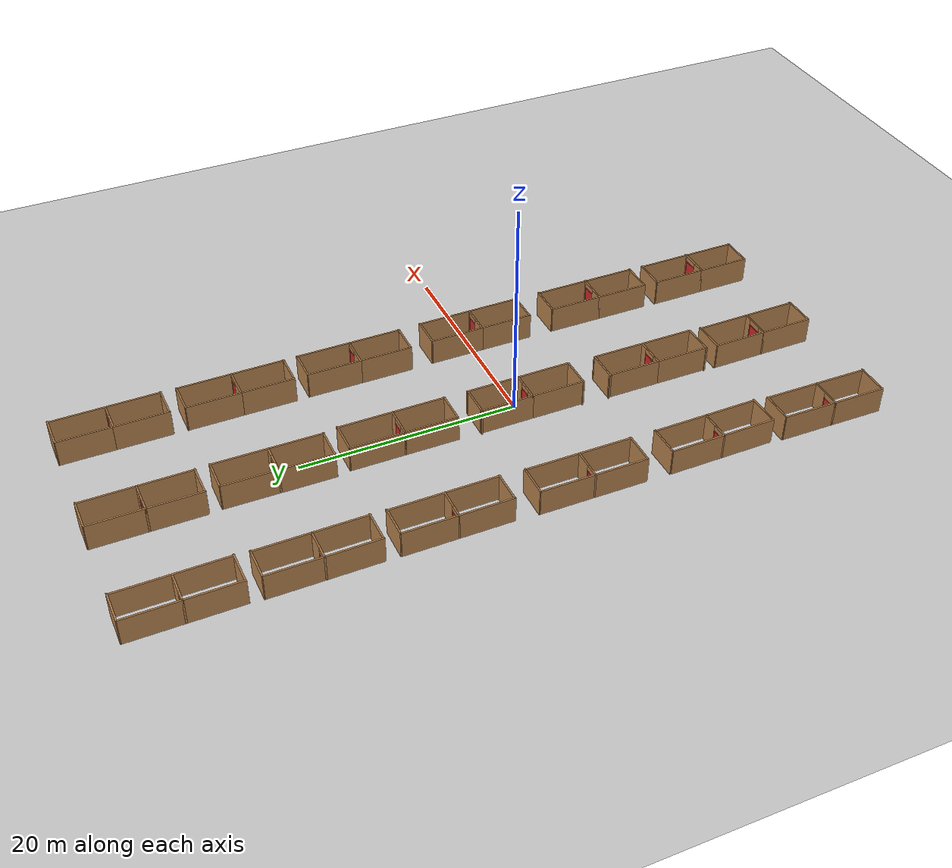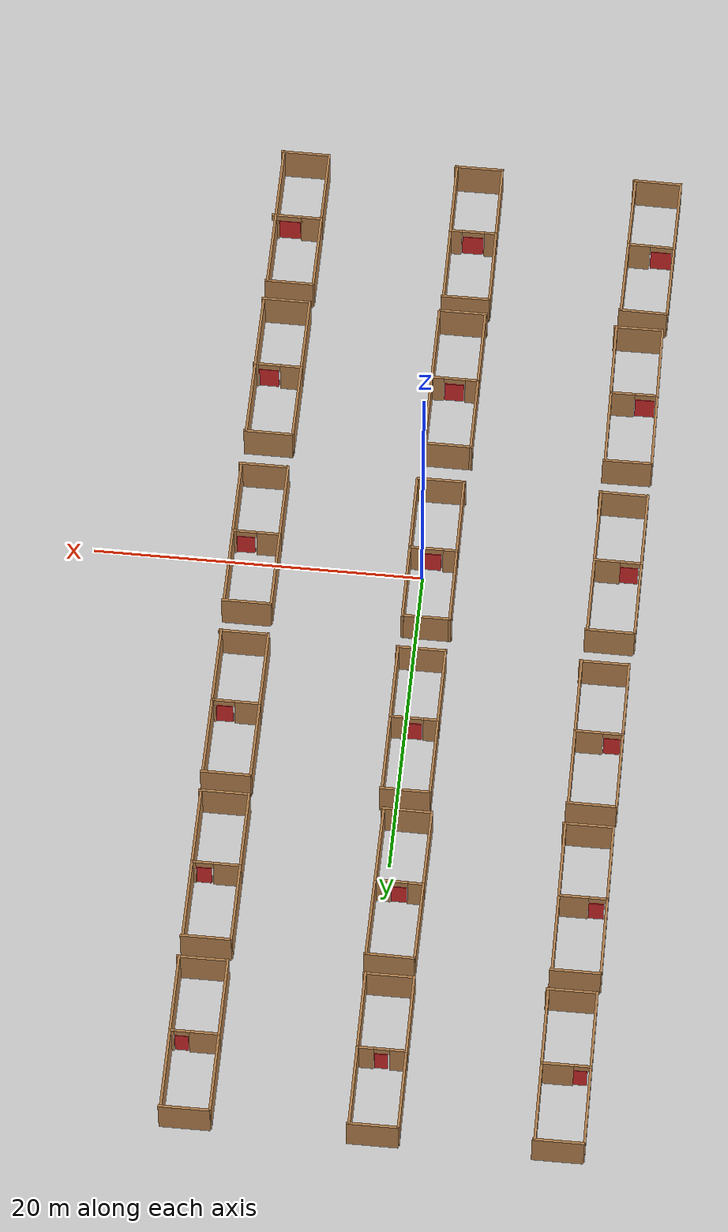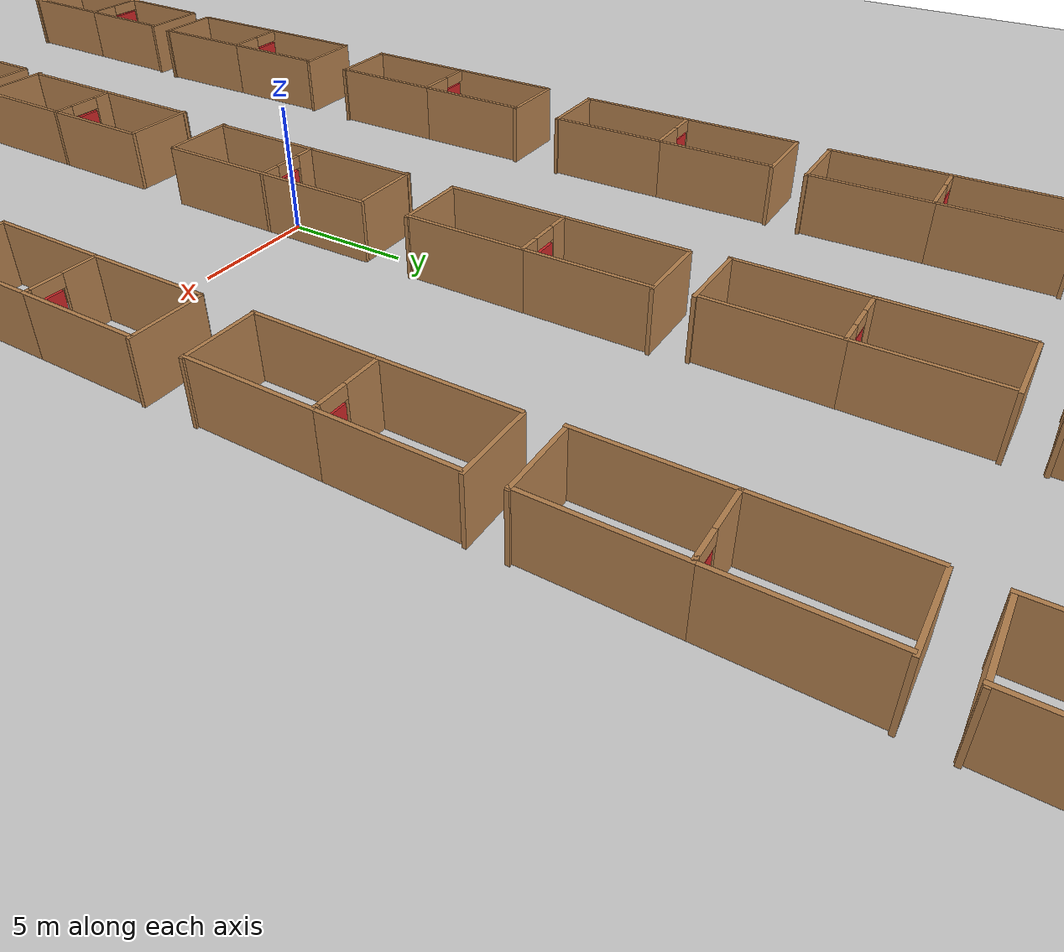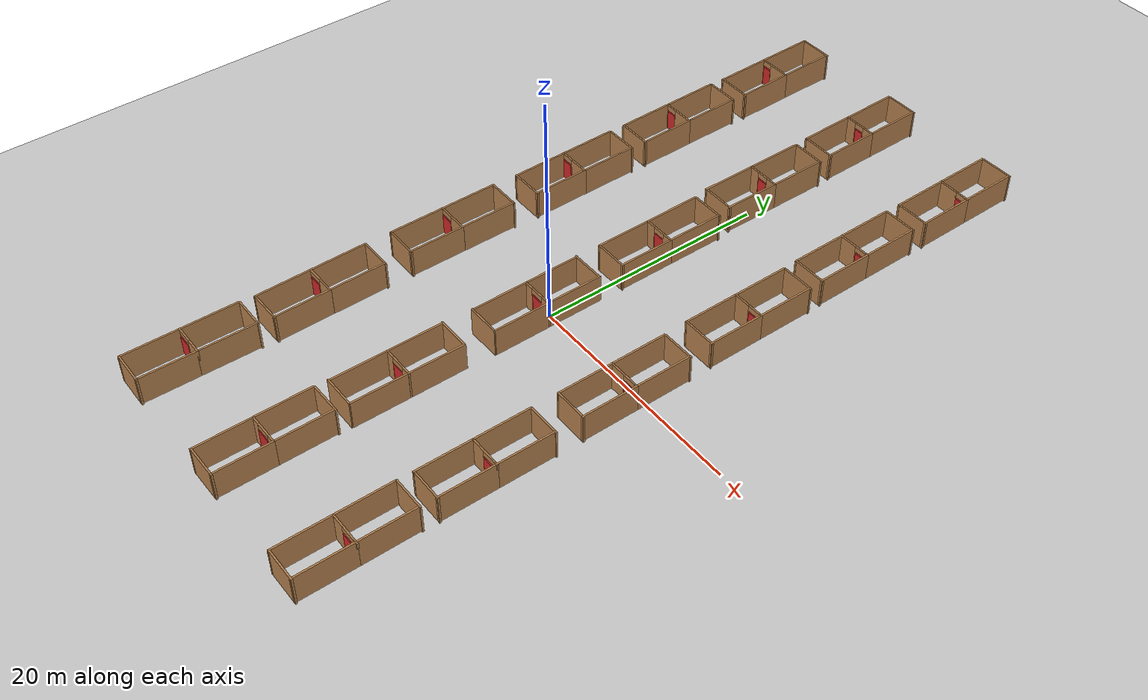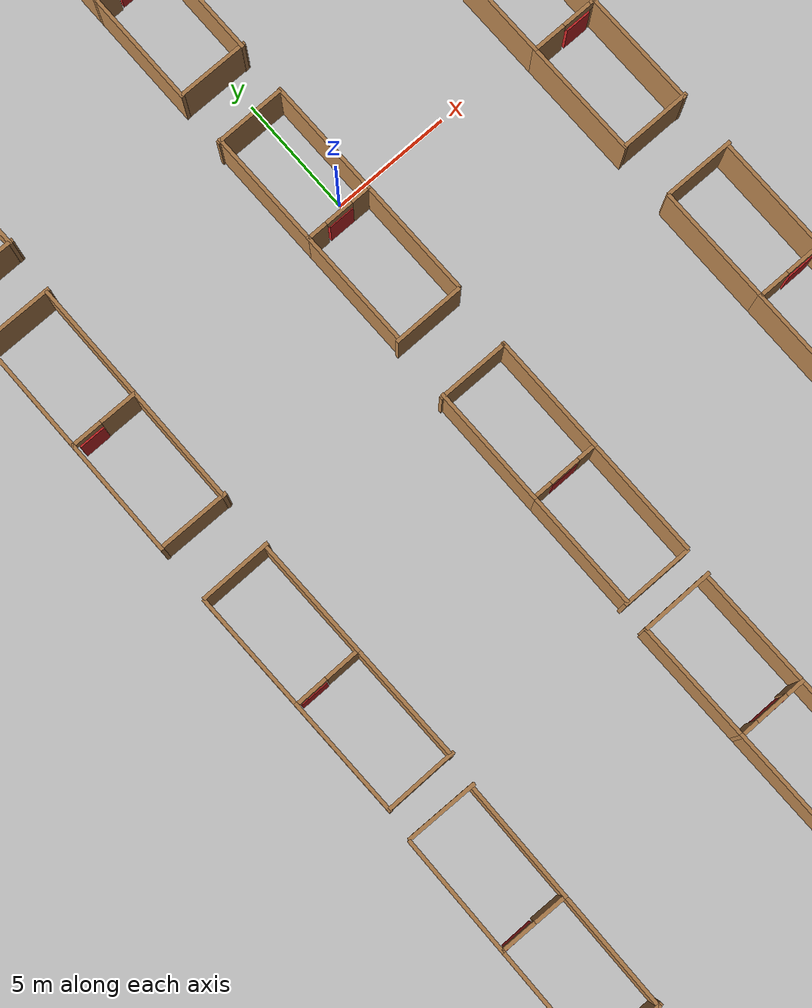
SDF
<sdf version="1.6">
 <world name="default">
  <model name="ground_plane">
   <static>1</static>
   <link name="link">
    <collision name="collision">
     <geometry><plane><normal>0 0 1</normal><size>100 100</size></plane></geometry>
     <surface><friction><ode><mu>100</mu><mu2>50</mu2></ode></friction></surface>
    </collision>
    <visual name="visual">
     <cast_shadows>0</cast_shadows>
     <geometry><plane><normal>0 0 1</normal><size>100 100</size></plane></geometry>
     <material>
      <script><uri>file://media/materials/scripts/gazebo.material</uri><name>Gazebo/Grey</name></script>
     </material>
    </visual>
   </link>
  </model>
  <light name="sun" type="directional">
   <pose>0 0 10 0 -0 0</pose>
   <diffuse>0.8 0.8 0.8 1</diffuse>
   <specular>0.2 0.2 0.2 1</specular>
   <attenuation>
    <range>1000</range>
    <constant>0.9</constant>
    <linear>0.01</linear>
    <quadratic>0.001</quadratic>
   </attenuation>
   <direction>-0.5 0.1 -0.9</direction>
   <spot><inner_angle>0</inner_angle><outer_angle>0</outer_angle><falloff>0</falloff></spot>
  </light>
  <scene><ambient>0.4 0.4 0.4 1</ambient><background>0 191 255 1</background><shadows>0</shadows></scene>
  <gravity>0 0 -9.8</gravity>
  <magnetic_field>6e-06 2.3e-05 -4.2e-05</magnetic_field>
  <atmosphere type="adiabatic"/>
  <physics name="default_physics" default="0" type="ode">
   <max_step_size>0.001</max_step_size>
   <real_time_factor>1</real_time_factor>
   <real_time_update_rate>1000</real_time_update_rate>
  </physics>
  <spherical_coordinates>
   <surface_model>EARTH_WGS84</surface_model>
   <latitude_deg>0</latitude_deg>
   <longitude_deg>0</longitude_deg>
   <elevation>0</elevation>
   <heading_deg>0</heading_deg>
  </spherical_coordinates>
  <model name="door_1">
   <link name="hinge">
    <inertial>
     <pose>-0.05 0 0 0 -0 0</pose>
     <mass>0.01</mass>
     <inertia><ixx>1</ixx><ixy>0</ixy><ixz>0</ixz><iyy>100</iyy><iyz>0</iyz><izz>1</izz></inertia>
    </inertial>
    <velocity_decay><linear>0</linear><angular>0</angular></velocity_decay>
   </link>
   <link name="door">
    <pose>0.1 -0.65 0.35 0 0 -1.57</pose>
    <inertial>
     <pose>0.1 -0.65 0.35 0 0 -1.57</pose>
     <mass>0.1</mass>
     <inertia><ixx>1</ixx><ixy>0</ixy><ixz>0</ixz><iyy>100</iyy><iyz>0</iyz><izz>1</izz></inertia>
    </inertial>
    <collision name="door_collision">
     <pose>0.1 -0.65 0.35 0 0 -1.57</pose>
     <geometry><box><size>1.1 0.15 1.8</size></box></geometry>
    </collision>
    <visual name="door_visual">
     <pose>0.1 -0.65 0.35 0 0 -1.57</pose>
     <geometry><box><size>1.1 0.15 1.8</size></box></geometry>
     <material><script><name>Gazebo/Red</name><uri>__default__</uri></script></material>
    </visual>
    <velocity_decay><linear>0</linear><angular>0</angular></velocity_decay>
   </link>
   <joint name="door_hinge" type="revolute">
    <child>door</child>
    <parent>hinge</parent>
    <pose>0.08 0 0 0 -0 0</pose>
    <axis>
     <xyz>0 0 1</xyz>
     <limit><lower>-1.57</lower><upper>1.57</upper><effort>0</effort><velocity>10</velocity></limit>
     <dynamics><spring_reference>0</spring_reference><spring_stiffness>0</spring_stiffness></dynamics>
     <use_parent_model_frame>0</use_parent_model_frame>
    </axis>
   </joint>
   <joint name="floor_link" type="revolute">
    <child>hinge</child>
    <parent>world</parent>
    <axis>
     <xyz>0 0 1</xyz>
     <limit><lower>0</lower><upper>0</upper><effort>0</effort><velocity>0</velocity></limit>
     <dynamics><spring_reference>0</spring_reference><spring_stiffness>0</spring_stiffness></dynamics>
     <use_parent_model_frame>0</use_parent_model_frame>
    </axis>
   </joint>
   <plugin name="door_plugin" filename="libdoor_plugin.so">
    <door_type>flip</door_type>
    <model_domain_space>door_</model_domain_space>
    <door_direction>clockwise</door_direction>
    <robotNamespace>/</robotNamespace>
   </plugin>
   <pose>-0 0 0.3 0 -0 0</pose>
  </model>
  <model name="door_2">
   <link name="hinge">
    <inertial>
     <pose>-0.05 0 0 0 -0 0</pose>
     <mass>0.01</mass>
     <inertia><ixx>1</ixx><ixy>0</ixy><ixz>0</ixz><iyy>100</iyy><iyz>0</iyz><izz>1</izz></inertia>
    </inertial>
    <velocity_decay><linear>0</linear><angular>0</angular></velocity_decay>
   </link>
   <link name="door">
    <pose>0.1 -0.6 0.35 0 0 -1.57</pose>
    <inertial>
     <pose>0.1 -0.6 0.35 0 0 -1.57</pose>
     <mass>0.1</mass>
     <inertia><ixx>1</ixx><ixy>0</ixy><ixz>0</ixz><iyy>100</iyy><iyz>0</iyz><izz>1</izz></inertia>
    </inertial>
    <collision name="door_collision">
     <pose>0.1 -0.6 0.35 0 0 -1.57</pose>
     <geometry><box><size>1 0.15 1.8</size></box></geometry>
    </collision>
    <visual name="door_visual">
     <pose>0.1 -0.6 0.35 0 0 -1.57</pose>
     <geometry><box><size>1 0.15 1.8</size></box></geometry>
     <material><script><name>Gazebo/Red</name><uri>__default__</uri></script></material>
    </visual>
    <velocity_decay><linear>0</linear><angular>0</angular></velocity_decay>
   </link>
   <joint name="door_hinge" type="revolute">
    <child>door</child>
    <parent>hinge</parent>
    <pose>0.08 0 0 0 -0 0</pose>
    <axis>
     <xyz>0 0 1</xyz>
     <limit><lower>-1.57</lower><upper>1.57</upper><effort>0</effort><velocity>10</velocity></limit>
     <dynamics><spring_reference>0</spring_reference><spring_stiffness>0</spring_stiffness></dynamics>
     <use_parent_model_frame>0</use_parent_model_frame>
    </axis>
   </joint>
   <joint name="floor_link" type="revolute">
    <child>hinge</child>
    <parent>world</parent>
    <axis>
     <xyz>0 0 1</xyz>
     <limit><lower>0</lower><upper>0</upper><effort>0</effort><velocity>0</velocity></limit>
     <dynamics><spring_reference>0</spring_reference><spring_stiffness>0</spring_stiffness></dynamics>
     <use_parent_model_frame>0</use_parent_model_frame>
    </axis>
   </joint>
   <plugin name="door_plugin" filename="libdoor_plugin.so">
    <door_type>flip</door_type>
    <model_domain_space>door_</model_domain_space>
    <door_direction>clockwise</door_direction>
    <robotNamespace>/</robotNamespace>
   </plugin>
   <pose>-0.060638 11.8346 0.3 0 -0 0</pose>
  </model>
  <model name="door_3">
   <link name="hinge">
    <inertial>
     <pose>-0.05 0 0 0 -0 0</pose>
     <mass>0.01</mass>
     <inertia><ixx>1</ixx><ixy>0</ixy><ixz>0</ixz><iyy>100</iyy><iyz>0</iyz><izz>1</izz></inertia>
    </inertial>
    <velocity_decay><linear>0</linear><angular>0</angular></velocity_decay>
   </link>
   <link name="door">
    <pose>0.1 -0.55 0.35 0 0 -1.57</pose>
    <inertial>
     <pose>0.1 -0.55 0.35 0 0 -1.57</pose>
     <mass>0.1</mass>
     <inertia><ixx>1</ixx><ixy>0</ixy><ixz>0</ixz><iyy>100</iyy><iyz>0</iyz><izz>1</izz></inertia>
    </inertial>
    <collision name="door_collision">
     <pose>0.1 -0.55 0.35 0 0 -1.57</pose>
     <geometry><box><size>0.9 0.15 1.8</size></box></geometry>
    </collision>
    <visual name="door_visual">
     <pose>0.1 -0.55 0.35 0 0 -1.57</pose>
     <geometry><box><size>0.9 0.15 1.8</size></box></geometry>
     <material><script><name>Gazebo/Red</name><uri>__default__</uri></script></material>
    </visual>
    <velocity_decay><linear>0</linear><angular>0</angular></velocity_decay>
   </link>
   <joint name="door_hinge" type="revolute">
    <child>door</child>
    <parent>hinge</parent>
    <pose>0.08 0 0 0 -0 0</pose>
    <axis>
     <xyz>0 0 1</xyz>
     <limit><lower>-1.57</lower><upper>1.57</upper><effort>0</effort><velocity>10</velocity></limit>
     <dynamics><spring_reference>0</spring_reference><spring_stiffness>0</spring_stiffness></dynamics>
     <use_parent_model_frame>0</use_parent_model_frame>
    </axis>
   </joint>
   <joint name="floor_link" type="revolute">
    <child>hinge</child>
    <parent>world</parent>
    <axis>
     <xyz>0 0 1</xyz>
     <limit><lower>0</lower><upper>0</upper><effort>0</effort><velocity>0</velocity></limit>
     <dynamics><spring_reference>0</spring_reference><spring_stiffness>0</spring_stiffness></dynamics>
     <use_parent_model_frame>0</use_parent_model_frame>
    </axis>
   </joint>
   <plugin name="door_plugin" filename="libdoor_plugin.so">
    <door_type>flip</door_type>
    <model_domain_space>door_</model_domain_space>
    <door_direction>clockwise</door_direction>
    <robotNamespace>/</robotNamespace>
   </plugin>
   <pose>-0.34012 22.8681 0.3 0 -0 0</pose>
  </model>
  <model name="door_4">
   <link name="hinge">
    <inertial>
     <pose>-0.05 0 0 0 -0 0</pose>
     <mass>0.01</mass>
     <inertia><ixx>1</ixx><ixy>0</ixy><ixz>0</ixz><iyy>100</iyy><iyz>0</iyz><izz>1</izz></inertia>
    </inertial>
    <velocity_decay><linear>0</linear><angular>0</angular></velocity_decay>
   </link>
   <link name="door">
    <pose>0.1 -0.5 0.35 0 0 -1.57</pose>
    <inertial>
     <pose>0.1 -0.5 0.35 0 0 -1.57</pose>
     <mass>0.1</mass>
     <inertia><ixx>1</ixx><ixy>0</ixy><ixz>0</ixz><iyy>100</iyy><iyz>0</iyz><izz>1</izz></inertia>
    </inertial>
    <collision name="door_collision">
     <pose>0.1 -0.5 0.35 0 0 -1.57</pose>
     <geometry><box><size>0.8 0.15 1.8</size></box></geometry>
    </collision>
    <visual name="door_visual">
     <pose>0.1 -0.5 0.35 0 0 -1.57</pose>
     <geometry><box><size>0.8 0.15 1.8</size></box></geometry>
     <material><script><name>Gazebo/Red</name><uri>__default__</uri></script></material>
    </visual>
    <velocity_decay><linear>0</linear><angular>0</angular></velocity_decay>
   </link>
   <joint name="door_hinge" type="revolute">
    <child>door</child>
    <parent>hinge</parent>
    <pose>0.08 0 0 0 -0 0</pose>
    <axis>
     <xyz>0 0 1</xyz>
     <limit><lower>-1.57</lower><upper>1.57</upper><effort>0</effort><velocity>10</velocity></limit>
     <dynamics><spring_reference>0</spring_reference><spring_stiffness>0</spring_stiffness></dynamics>
     <use_parent_model_frame>0</use_parent_model_frame>
    </axis>
   </joint>
   <joint name="floor_link" type="revolute">
    <child>hinge</child>
    <parent>world</parent>
    <axis>
     <xyz>0 0 1</xyz>
     <limit><lower>0</lower><upper>0</upper><effort>0</effort><velocity>0</velocity></limit>
     <dynamics><spring_reference>0</spring_reference><spring_stiffness>0</spring_stiffness></dynamics>
     <use_parent_model_frame>0</use_parent_model_frame>
    </axis>
   </joint>
   <plugin name="door_plugin" filename="libdoor_plugin.so">
    <door_type>flip</door_type>
    <model_domain_space>door_</model_domain_space>
    <door_direction>clockwise</door_direction>
    <robotNamespace>/</robotNamespace>
   </plugin>
   <pose>-0.425173 33.8346 0.3 0 -0 0</pose>
  </model>
  <model name="door_5">
   <link name="hinge">
    <inertial>
     <pose>-0.05 0 0 0 -0 0</pose>
     <mass>0.01</mass>
     <inertia><ixx>1</ixx><ixy>0</ixy><ixz>0</ixz><iyy>100</iyy><iyz>0</iyz><izz>1</izz></inertia>
    </inertial>
    <velocity_decay><linear>0</linear><angular>0</angular></velocity_decay>
   </link>
   <link name="door">
    <pose>0.1 -0.7 0.35 0 0 -1.57</pose>
    <inertial>
     <pose>0.1 -0.7 0.35 0 0 -1.57</pose>
     <mass>0.1</mass>
     <inertia><ixx>1</ixx><ixy>0</ixy><ixz>0</ixz><iyy>100</iyy><iyz>0</iyz><izz>1</izz></inertia>
    </inertial>
    <collision name="door_collision">
     <pose>0.1 -0.7 0.35 0 0 -1.57</pose>
     <geometry><box><size>1.2 0.15 1.8</size></box></geometry>
    </collision>
    <visual name="door_visual">
     <pose>0.1 -0.7 0.35 0 0 -1.57</pose>
     <geometry><box><size>1.2 0.15 1.8</size></box></geometry>
     <material><script><name>Gazebo/Red</name><uri>__default__</uri></script></material>
    </visual>
    <velocity_decay><linear>0</linear><angular>0</angular></velocity_decay>
   </link>
   <joint name="door_hinge" type="revolute">
    <child>door</child>
    <parent>hinge</parent>
    <pose>0.08 0 0 0 -0 0</pose>
    <axis>
     <xyz>0 0 1</xyz>
     <limit><lower>-1.57</lower><upper>1.57</upper><effort>0</effort><velocity>10</velocity></limit>
     <dynamics><spring_reference>0</spring_reference><spring_stiffness>0</spring_stiffness></dynamics>
     <use_parent_model_frame>0</use_parent_model_frame>
    </axis>
   </joint>
   <joint name="floor_link" type="revolute">
    <child>hinge</child>
    <parent>world</parent>
    <axis>
     <xyz>0 0 1</xyz>
     <limit><lower>0</lower><upper>0</upper><effort>0</effort><velocity>0</velocity></limit>
     <dynamics><spring_reference>0</spring_reference><spring_stiffness>0</spring_stiffness></dynamics>
     <use_parent_model_frame>0</use_parent_model_frame>
    </axis>
   </joint>
   <plugin name="door_plugin" filename="libdoor_plugin.so">
    <door_type>flip</door_type>
    <model_domain_space>door_</model_domain_space>
    <door_direction>clockwise</door_direction>
    <robotNamespace>/</robotNamespace>
   </plugin>
   <pose>-0.138625 -12.2538 0.3 0 -0 0</pose>
  </model>
  <model name="door_6">
   <link name="hinge">
    <inertial>
     <pose>-0.05 0 0 0 -0 0</pose>
     <mass>0.01</mass>
     <inertia><ixx>1</ixx><ixy>0</ixy><ixz>0</ixz><iyy>100</iyy><iyz>0</iyz><izz>1</izz></inertia>
    </inertial>
    <velocity_decay><linear>0</linear><angular>0</angular></velocity_decay>
   </link>
   <link name="door">
    <pose>0.1 -0.75 0.35 0 0 -1.57</pose>
    <inertial>
     <pose>0.1 -0.75 0.35 0 0 -1.57</pose>
     <mass>0.1</mass>
     <inertia><ixx>1</ixx><ixy>0</ixy><ixz>0</ixz><iyy>100</iyy><iyz>0</iyz><izz>1</izz></inertia>
    </inertial>
    <collision name="door_collision">
     <pose>0.1 -0.75 0.35 0 0 -1.57</pose>
     <geometry><box><size>1.3 0.15 1.8</size></box></geometry>
    </collision>
    <visual name="door_visual">
     <pose>0.1 -0.75 0.35 0 0 -1.57</pose>
     <geometry><box><size>1.3 0.15 1.8</size></box></geometry>
     <material><script><name>Gazebo/Red</name><uri>__default__</uri></script></material>
    </visual>
    <velocity_decay><linear>0</linear><angular>0</angular></velocity_decay>
   </link>
   <joint name="door_hinge" type="revolute">
    <child>door</child>
    <parent>hinge</parent>
    <pose>0.08 0 0 0 -0 0</pose>
    <axis>
     <xyz>0 0 1</xyz>
     <limit><lower>-1.57</lower><upper>1.57</upper><effort>0</effort><velocity>10</velocity></limit>
     <dynamics><spring_reference>0</spring_reference><spring_stiffness>0</spring_stiffness></dynamics>
     <use_parent_model_frame>0</use_parent_model_frame>
    </axis>
   </joint>
   <joint name="floor_link" type="revolute">
    <child>hinge</child>
    <parent>world</parent>
    <axis>
     <xyz>0 0 1</xyz>
     <limit><lower>0</lower><upper>0</upper><effort>0</effort><velocity>0</velocity></limit>
     <dynamics><spring_reference>0</spring_reference><spring_stiffness>0</spring_stiffness></dynamics>
     <use_parent_model_frame>0</use_parent_model_frame>
    </axis>
   </joint>
   <plugin name="door_plugin" filename="libdoor_plugin.so">
    <door_type>flip</door_type>
    <model_domain_space>door_</model_domain_space>
    <door_direction>clockwise</door_direction>
    <robotNamespace>/</robotNamespace>
   </plugin>
   <pose>-0.228773 -23.1883 0.3 0 -0 0</pose>
  </model>
  <model name="door_7">
   <link name="hinge">
    <inertial>
     <pose>-0.05 0 0 0 -0 0</pose>
     <mass>0.01</mass>
     <inertia><ixx>1</ixx><ixy>0</ixy><ixz>0</ixz><iyy>100</iyy><iyz>0</iyz><izz>1</izz></inertia>
    </inertial>
    <velocity_decay><linear>0</linear><angular>0</angular></velocity_decay>
   </link>
   <link name="door">
    <pose>0.1 -0.65 0.35 0 0 -1.57</pose>
    <inertial>
     <pose>0.1 -0.65 0.35 0 0 -1.57</pose>
     <mass>0.1</mass>
     <inertia><ixx>1</ixx><ixy>0</ixy><ixz>0</ixz><iyy>100</iyy><iyz>0</iyz><izz>1</izz></inertia>
    </inertial>
    <collision name="door_collision">
     <pose>0.1 -0.65 0.35 0 0 -1.57</pose>
     <geometry><box><size>1.1 0.15 1.8</size></box></geometry>
    </collision>
    <visual name="door_visual">
     <pose>0.1 -0.65 0.35 0 0 -1.57</pose>
     <geometry><box><size>1.1 0.15 1.8</size></box></geometry>
     <material><script><name>Gazebo/Red</name><uri>__default__</uri></script></material>
    </visual>
    <velocity_decay><linear>0</linear><angular>0</angular></velocity_decay>
   </link>
   <joint name="door_hinge" type="revolute">
    <child>door</child>
    <parent>hinge</parent>
    <pose>0.08 0 0 0 -0 0</pose>
    <axis>
     <xyz>0 0 1</xyz>
     <limit><lower>-1.57</lower><upper>1.57</upper><effort>0</effort><velocity>10</velocity></limit>
     <dynamics><spring_reference>0</spring_reference><spring_stiffness>0</spring_stiffness></dynamics>
     <use_parent_model_frame>0</use_parent_model_frame>
    </axis>
   </joint>
   <joint name="floor_link" type="revolute">
    <child>hinge</child>
    <parent>world</parent>
    <axis>
     <xyz>0 0 1</xyz>
     <limit><lower>0</lower><upper>0</upper><effort>0</effort><velocity>0</velocity></limit>
     <dynamics><spring_reference>0</spring_reference><spring_stiffness>0</spring_stiffness></dynamics>
     <use_parent_model_frame>0</use_parent_model_frame>
    </axis>
   </joint>
   <plugin name="door_plugin" filename="libdoor_plugin.so">
    <door_type>flip</door_type>
    <model_domain_space>door_</model_domain_space>
    <door_direction>clockwise</door_direction>
    <robotNamespace>/</robotNamespace>
   </plugin>
   <pose>11.3504 -0.115257 0.3 0 -0 0</pose>
  </model>
  <model name="door_8">
   <link name="hinge">
    <inertial>
     <pose>-0.05 0 0 0 -0 0</pose>
     <mass>0.01</mass>
     <inertia><ixx>1</ixx><ixy>0</ixy><ixz>0</ixz><iyy>100</iyy><iyz>0</iyz><izz>1</izz></inertia>
    </inertial>
    <velocity_decay><linear>0</linear><angular>0</angular></velocity_decay>
   </link>
   <link name="door">
    <pose>0.1 -0.7 0.35 0 0 -1.57</pose>
    <inertial>
     <pose>0.1 -0.7 0.35 0 0 -1.57</pose>
     <mass>0.1</mass>
     <inertia><ixx>1</ixx><ixy>0</ixy><ixz>0</ixz><iyy>100</iyy><iyz>0</iyz><izz>1</izz></inertia>
    </inertial>
    <collision name="door_collision">
     <pose>0.1 -0.7 0.35 0 0 -1.57</pose>
     <geometry><box><size>1.2 0.15 1.8</size></box></geometry>
    </collision>
    <visual name="door_visual">
     <pose>0.1 -0.7 0.35 0 0 -1.57</pose>
     <geometry><box><size>1.2 0.15 1.8</size></box></geometry>
     <material><script><name>Gazebo/Red</name><uri>__default__</uri></script></material>
    </visual>
    <velocity_decay><linear>0</linear><angular>0</angular></velocity_decay>
   </link>
   <joint name="door_hinge" type="revolute">
    <child>door</child>
    <parent>hinge</parent>
    <pose>0.08 0 0 0 -0 0</pose>
    <axis>
     <xyz>0 0 1</xyz>
     <limit><lower>-1.57</lower><upper>1.57</upper><effort>0</effort><velocity>10</velocity></limit>
     <dynamics><spring_reference>0</spring_reference><spring_stiffness>0</spring_stiffness></dynamics>
     <use_parent_model_frame>0</use_parent_model_frame>
    </axis>
   </joint>
   <joint name="floor_link" type="revolute">
    <child>hinge</child>
    <parent>world</parent>
    <axis>
     <xyz>0 0 1</xyz>
     <limit><lower>0</lower><upper>0</upper><effort>0</effort><velocity>0</velocity></limit>
     <dynamics><spring_reference>0</spring_reference><spring_stiffness>0</spring_stiffness></dynamics>
     <use_parent_model_frame>0</use_parent_model_frame>
    </axis>
   </joint>
   <plugin name="door_plugin" filename="libdoor_plugin.so">
    <door_type>flip</door_type>
    <model_domain_space>door_</model_domain_space>
    <door_direction>clockwise</door_direction>
    <robotNamespace>/</robotNamespace>
   </plugin>
   <pose>11.3057 -12.1813 0.3 0 -0 0</pose>
  </model>
  <model name="door_9">
   <link name="hinge">
    <inertial>
     <pose>-0.05 0 0 0 -0 0</pose>
     <mass>0.01</mass>
     <inertia><ixx>1</ixx><ixy>0</ixy><ixz>0</ixz><iyy>100</iyy><iyz>0</iyz><izz>1</izz></inertia>
    </inertial>
    <velocity_decay><linear>0</linear><angular>0</angular></velocity_decay>
   </link>
   <link name="door">
    <pose>0.1 -0.75 0.35 0 0 -1.57</pose>
    <inertial>
     <pose>0.1 -0.75 0.35 0 0 -1.57</pose>
     <mass>0.1</mass>
     <inertia><ixx>1</ixx><ixy>0</ixy><ixz>0</ixz><iyy>100</iyy><iyz>0</iyz><izz>1</izz></inertia>
    </inertial>
    <collision name="door_collision">
     <pose>0.1 -0.75 0.35 0 0 -1.57</pose>
     <geometry><box><size>1.3 0.15 1.8</size></box></geometry>
    </collision>
    <visual name="door_visual">
     <pose>0.1 -0.75 0.35 0 0 -1.57</pose>
     <geometry><box><size>1.3 0.15 1.8</size></box></geometry>
     <material><script><name>Gazebo/Red</name><uri>__default__</uri></script></material>
    </visual>
    <velocity_decay><linear>0</linear><angular>0</angular></velocity_decay>
   </link>
   <joint name="door_hinge" type="revolute">
    <child>door</child>
    <parent>hinge</parent>
    <pose>0.08 0 0 0 -0 0</pose>
    <axis>
     <xyz>0 0 1</xyz>
     <limit><lower>-1.57</lower><upper>1.57</upper><effort>0</effort><velocity>10</velocity></limit>
     <dynamics><spring_reference>0</spring_reference><spring_stiffness>0</spring_stiffness></dynamics>
     <use_parent_model_frame>0</use_parent_model_frame>
    </axis>
   </joint>
   <joint name="floor_link" type="revolute">
    <child>hinge</child>
    <parent>world</parent>
    <axis>
     <xyz>0 0 1</xyz>
     <limit><lower>0</lower><upper>0</upper><effort>0</effort><velocity>0</velocity></limit>
     <dynamics><spring_reference>0</spring_reference><spring_stiffness>0</spring_stiffness></dynamics>
     <use_parent_model_frame>0</use_parent_model_frame>
    </axis>
   </joint>
   <plugin name="door_plugin" filename="libdoor_plugin.so">
    <door_type>flip</door_type>
    <model_domain_space>door_</model_domain_space>
    <door_direction>clockwise</door_direction>
    <robotNamespace>/</robotNamespace>
   </plugin>
   <pose>11.2429 -23.2301 0.3 0 -0 0</pose>
  </model>
  <model name="door_10">
   <link name="hinge">
    <inertial>
     <pose>-0.05 0 0 0 -0 0</pose>
     <mass>0.01</mass>
     <inertia><ixx>1</ixx><ixy>0</ixy><ixz>0</ixz><iyy>100</iyy><iyz>0</iyz><izz>1</izz></inertia>
    </inertial>
    <velocity_decay><linear>0</linear><angular>0</angular></velocity_decay>
   </link>
   <link name="door">
    <pose>0.1 -0.6 0.35 0 0 -1.57</pose>
    <inertial>
     <pose>0.1 -0.6 0.35 0 0 -1.57</pose>
     <mass>0.1</mass>
     <inertia><ixx>1</ixx><ixy>0</ixy><ixz>0</ixz><iyy>100</iyy><iyz>0</iyz><izz>1</izz></inertia>
    </inertial>
    <collision name="door_collision">
     <pose>0.1 -0.6 0.35 0 0 -1.57</pose>
     <geometry><box><size>1 0.15 1.8</size></box></geometry>
    </collision>
    <visual name="door_visual">
     <pose>0.1 -0.6 0.35 0 0 -1.57</pose>
     <geometry><box><size>1 0.15 1.8</size></box></geometry>
     <material><script><name>Gazebo/Red</name><uri>__default__</uri></script></material>
    </visual>
    <velocity_decay><linear>0</linear><angular>0</angular></velocity_decay>
   </link>
   <joint name="door_hinge" type="revolute">
    <child>door</child>
    <parent>hinge</parent>
    <pose>0.08 0 0 0 -0 0</pose>
    <axis>
     <xyz>0 0 1</xyz>
     <limit><lower>-1.57</lower><upper>1.57</upper><effort>0</effort><velocity>10</velocity></limit>
     <dynamics><spring_reference>0</spring_reference><spring_stiffness>0</spring_stiffness></dynamics>
     <use_parent_model_frame>0</use_parent_model_frame>
    </axis>
   </joint>
   <joint name="floor_link" type="revolute">
    <child>hinge</child>
    <parent>world</parent>
    <axis>
     <xyz>0 0 1</xyz>
     <limit><lower>0</lower><upper>0</upper><effort>0</effort><velocity>0</velocity></limit>
     <dynamics><spring_reference>0</spring_reference><spring_stiffness>0</spring_stiffness></dynamics>
     <use_parent_model_frame>0</use_parent_model_frame>
    </axis>
   </joint>
   <plugin name="door_plugin" filename="libdoor_plugin.so">
    <door_type>flip</door_type>
    <model_domain_space>door_</model_domain_space>
    <door_direction>clockwise</door_direction>
    <robotNamespace>/</robotNamespace>
   </plugin>
   <pose>11.2661 11.7432 0.3 0 -0 0</pose>
  </model>
  <model name="door_11">
   <link name="hinge">
    <inertial>
     <pose>-0.05 0 0 0 -0 0</pose>
     <mass>0.01</mass>
     <inertia><ixx>1</ixx><ixy>0</ixy><ixz>0</ixz><iyy>100</iyy><iyz>0</iyz><izz>1</izz></inertia>
    </inertial>
    <velocity_decay><linear>0</linear><angular>0</angular></velocity_decay>
   </link>
   <link name="door">
    <pose>0.1 -0.55 0.35 0 0 -1.57</pose>
    <inertial>
     <pose>0.1 -0.55 0.35 0 0 -1.57</pose>
     <mass>0.1</mass>
     <inertia><ixx>1</ixx><ixy>0</ixy><ixz>0</ixz><iyy>100</iyy><iyz>0</iyz><izz>1</izz></inertia>
    </inertial>
    <collision name="door_collision">
     <pose>0.1 -0.55 0.35 0 0 -1.57</pose>
     <geometry><box><size>0.9 0.15 1.8</size></box></geometry>
    </collision>
    <visual name="door_visual">
     <pose>0.1 -0.55 0.35 0 0 -1.57</pose>
     <geometry><box><size>0.9 0.15 1.8</size></box></geometry>
     <material><script><name>Gazebo/Red</name><uri>__default__</uri></script></material>
    </visual>
    <velocity_decay><linear>0</linear><angular>0</angular></velocity_decay>
   </link>
   <joint name="door_hinge" type="revolute">
    <child>door</child>
    <parent>hinge</parent>
    <pose>0.08 0 0 0 -0 0</pose>
    <axis>
     <xyz>0 0 1</xyz>
     <limit><lower>-1.57</lower><upper>1.57</upper><effort>0</effort><velocity>10</velocity></limit>
     <dynamics><spring_reference>0</spring_reference><spring_stiffness>0</spring_stiffness></dynamics>
     <use_parent_model_frame>0</use_parent_model_frame>
    </axis>
   </joint>
   <joint name="floor_link" type="revolute">
    <child>hinge</child>
    <parent>world</parent>
    <axis>
     <xyz>0 0 1</xyz>
     <limit><lower>0</lower><upper>0</upper><effort>0</effort><velocity>0</velocity></limit>
     <dynamics><spring_reference>0</spring_reference><spring_stiffness>0</spring_stiffness></dynamics>
     <use_parent_model_frame>0</use_parent_model_frame>
    </axis>
   </joint>
   <plugin name="door_plugin" filename="libdoor_plugin.so">
    <door_type>flip</door_type>
    <model_domain_space>door_</model_domain_space>
    <door_direction>clockwise</door_direction>
    <robotNamespace>/</robotNamespace>
   </plugin>
   <pose>11.2017 22.7287 0.3 0 -0 0</pose>
  </model>
  <model name="door_12">
   <link name="hinge">
    <inertial>
     <pose>-0.05 0 0 0 -0 0</pose>
     <mass>0.01</mass>
     <inertia><ixx>1</ixx><ixy>0</ixy><ixz>0</ixz><iyy>100</iyy><iyz>0</iyz><izz>1</izz></inertia>
    </inertial>
    <velocity_decay><linear>0</linear><angular>0</angular></velocity_decay>
   </link>
   <link name="door">
    <pose>0.1 -0.5 0.35 0 0 -1.57</pose>
    <inertial>
     <pose>0.1 -0.5 0.35 0 0 -1.57</pose>
     <mass>0.1</mass>
     <inertia><ixx>1</ixx><ixy>0</ixy><ixz>0</ixz><iyy>100</iyy><iyz>0</iyz><izz>1</izz></inertia>
    </inertial>
    <collision name="door_collision">
     <pose>0.1 -0.5 0.35 0 0 -1.57</pose>
     <geometry><box><size>0.8 0.15 1.8</size></box></geometry>
    </collision>
    <visual name="door_visual">
     <pose>0.1 -0.5 0.35 0 0 -1.57</pose>
     <geometry><box><size>0.8 0.15 1.8</size></box></geometry>
     <material><script><name>Gazebo/Red</name><uri>__default__</uri></script></material>
    </visual>
    <velocity_decay><linear>0</linear><angular>0</angular></velocity_decay>
   </link>
   <joint name="door_hinge" type="revolute">
    <child>door</child>
    <parent>hinge</parent>
    <pose>0.08 0 0 0 -0 0</pose>
    <axis>
     <xyz>0 0 1</xyz>
     <limit><lower>-1.57</lower><upper>1.57</upper><effort>0</effort><velocity>10</velocity></limit>
     <dynamics><spring_reference>0</spring_reference><spring_stiffness>0</spring_stiffness></dynamics>
     <use_parent_model_frame>0</use_parent_model_frame>
    </axis>
   </joint>
   <joint name="floor_link" type="revolute">
    <child>hinge</child>
    <parent>world</parent>
    <axis>
     <xyz>0 0 1</xyz>
     <limit><lower>0</lower><upper>0</upper><effort>0</effort><velocity>0</velocity></limit>
     <dynamics><spring_reference>0</spring_reference><spring_stiffness>0</spring_stiffness></dynamics>
     <use_parent_model_frame>0</use_parent_model_frame>
    </axis>
   </joint>
   <plugin name="door_plugin" filename="libdoor_plugin.so">
    <door_type>flip</door_type>
    <model_domain_space>door_</model_domain_space>
    <door_direction>clockwise</door_direction>
    <robotNamespace>/</robotNamespace>
   </plugin>
   <pose>11.1979 33.8103 0.3 0 -0 0</pose>
  </model>
  <model name="door_13">
   <link name="hinge">
    <inertial>
     <pose>-0.05 0 0 0 -0 0</pose>
     <mass>0.01</mass>
     <inertia><ixx>1</ixx><ixy>0</ixy><ixz>0</ixz><iyy>100</iyy><iyz>0</iyz><izz>1</izz></inertia>
    </inertial>
    <velocity_decay><linear>0</linear><angular>0</angular></velocity_decay>
   </link>
   <link name="door">
    <pose>0.1 -0.75 0.35 0 0 -1.57</pose>
    <inertial>
     <pose>0.1 -0.75 0.35 0 0 -1.57</pose>
     <mass>0.1</mass>
     <inertia><ixx>1</ixx><ixy>0</ixy><ixz>0</ixz><iyy>100</iyy><iyz>0</iyz><izz>1</izz></inertia>
    </inertial>
    <collision name="door_collision">
     <pose>0.1 -0.75 0.35 0 0 -1.57</pose>
     <geometry><box><size>1.3 0.15 1.8</size></box></geometry>
    </collision>
    <visual name="door_visual">
     <pose>0.1 -0.75 0.35 0 0 -1.57</pose>
     <geometry><box><size>1.3 0.15 1.8</size></box></geometry>
     <material><script><name>Gazebo/Red</name><uri>__default__</uri></script></material>
    </visual>
    <velocity_decay><linear>0</linear><angular>0</angular></velocity_decay>
   </link>
   <joint name="door_hinge" type="revolute">
    <child>door</child>
    <parent>hinge</parent>
    <pose>0.08 0 0 0 -0 0</pose>
    <axis>
     <xyz>0 0 1</xyz>
     <limit><lower>-1.57</lower><upper>1.57</upper><effort>0</effort><velocity>10</velocity></limit>
     <dynamics><spring_reference>0</spring_reference><spring_stiffness>0</spring_stiffness></dynamics>
     <use_parent_model_frame>0</use_parent_model_frame>
    </axis>
   </joint>
   <joint name="floor_link" type="revolute">
    <child>hinge</child>
    <parent>world</parent>
    <axis>
     <xyz>0 0 1</xyz>
     <limit><lower>0</lower><upper>0</upper><effort>0</effort><velocity>0</velocity></limit>
     <dynamics><spring_reference>0</spring_reference><spring_stiffness>0</spring_stiffness></dynamics>
     <use_parent_model_frame>0</use_parent_model_frame>
    </axis>
   </joint>
   <plugin name="door_plugin" filename="libdoor_plugin.so">
    <door_type>flip</door_type>
    <model_domain_space>door_</model_domain_space>
    <door_direction>clockwise</door_direction>
    <robotNamespace>/</robotNamespace>
   </plugin>
   <pose>-11.9963 -23.2247 0.3 0 -0 0</pose>
  </model>
  <model name="door_14">
   <link name="hinge">
    <inertial>
     <pose>-0.05 0 0 0 -0 0</pose>
     <mass>0.01</mass>
     <inertia><ixx>1</ixx><ixy>0</ixy><ixz>0</ixz><iyy>100</iyy><iyz>0</iyz><izz>1</izz></inertia>
    </inertial>
    <velocity_decay><linear>0</linear><angular>0</angular></velocity_decay>
   </link>
   <link name="door">
    <pose>0.1 -0.7 0.35 0 0 -1.57</pose>
    <inertial>
     <pose>0.1 -0.7 0.35 0 0 -1.57</pose>
     <mass>0.1</mass>
     <inertia><ixx>1</ixx><ixy>0</ixy><ixz>0</ixz><iyy>100</iyy><iyz>0</iyz><izz>1</izz></inertia>
    </inertial>
    <collision name="door_collision">
     <pose>0.1 -0.7 0.35 0 0 -1.57</pose>
     <geometry><box><size>1.2 0.15 1.8</size></box></geometry>
    </collision>
    <visual name="door_visual">
     <pose>0.1 -0.7 0.35 0 0 -1.57</pose>
     <geometry><box><size>1.2 0.15 1.8</size></box></geometry>
     <material><script><name>Gazebo/Red</name><uri>__default__</uri></script></material>
    </visual>
    <velocity_decay><linear>0</linear><angular>0</angular></velocity_decay>
   </link>
   <joint name="door_hinge" type="revolute">
    <child>door</child>
    <parent>hinge</parent>
    <pose>0.08 0 0 0 -0 0</pose>
    <axis>
     <xyz>0 0 1</xyz>
     <limit><lower>-1.57</lower><upper>1.57</upper><effort>0</effort><velocity>10</velocity></limit>
     <dynamics><spring_reference>0</spring_reference><spring_stiffness>0</spring_stiffness></dynamics>
     <use_parent_model_frame>0</use_parent_model_frame>
    </axis>
   </joint>
   <joint name="floor_link" type="revolute">
    <child>hinge</child>
    <parent>world</parent>
    <axis>
     <xyz>0 0 1</xyz>
     <limit><lower>0</lower><upper>0</upper><effort>0</effort><velocity>0</velocity></limit>
     <dynamics><spring_reference>0</spring_reference><spring_stiffness>0</spring_stiffness></dynamics>
     <use_parent_model_frame>0</use_parent_model_frame>
    </axis>
   </joint>
   <plugin name="door_plugin" filename="libdoor_plugin.so">
    <door_type>flip</door_type>
    <model_domain_space>door_</model_domain_space>
    <door_direction>clockwise</door_direction>
    <robotNamespace>/</robotNamespace>
   </plugin>
   <pose>-11.8998 -12.2711 0.3 0 -0 0</pose>
  </model>
  <model name="door_15">
   <link name="hinge">
    <inertial>
     <pose>-0.05 0 0 0 -0 0</pose>
     <mass>0.01</mass>
     <inertia><ixx>1</ixx><ixy>0</ixy><ixz>0</ixz><iyy>100</iyy><iyz>0</iyz><izz>1</izz></inertia>
    </inertial>
    <velocity_decay><linear>0</linear><angular>0</angular></velocity_decay>
   </link>
   <link name="door">
    <pose>0.1 -0.65 0.35 0 0 -1.57</pose>
    <inertial>
     <pose>0.1 -0.65 0.35 0 0 -1.57</pose>
     <mass>0.1</mass>
     <inertia><ixx>1</ixx><ixy>0</ixy><ixz>0</ixz><iyy>100</iyy><iyz>0</iyz><izz>1</izz></inertia>
    </inertial>
    <collision name="door_collision">
     <pose>0.1 -0.65 0.35 0 0 -1.57</pose>
     <geometry><box><size>1.1 0.15 1.8</size></box></geometry>
    </collision>
    <visual name="door_visual">
     <pose>0.1 -0.65 0.35 0 0 -1.57</pose>
     <geometry><box><size>1.1 0.15 1.8</size></box></geometry>
     <material><script><name>Gazebo/Red</name><uri>__default__</uri></script></material>
    </visual>
    <velocity_decay><linear>0</linear><angular>0</angular></velocity_decay>
   </link>
   <joint name="door_hinge" type="revolute">
    <child>door</child>
    <parent>hinge</parent>
    <pose>0.08 0 0 0 -0 0</pose>
    <axis>
     <xyz>0 0 1</xyz>
     <limit><lower>-1.57</lower><upper>1.57</upper><effort>0</effort><velocity>10</velocity></limit>
     <dynamics><spring_reference>0</spring_reference><spring_stiffness>0</spring_stiffness></dynamics>
     <use_parent_model_frame>0</use_parent_model_frame>
    </axis>
   </joint>
   <joint name="floor_link" type="revolute">
    <child>hinge</child>
    <parent>world</parent>
    <axis>
     <xyz>0 0 1</xyz>
     <limit><lower>0</lower><upper>0</upper><effort>0</effort><velocity>0</velocity></limit>
     <dynamics><spring_reference>0</spring_reference><spring_stiffness>0</spring_stiffness></dynamics>
     <use_parent_model_frame>0</use_parent_model_frame>
    </axis>
   </joint>
   <plugin name="door_plugin" filename="libdoor_plugin.so">
    <door_type>flip</door_type>
    <model_domain_space>door_</model_domain_space>
    <door_direction>clockwise</door_direction>
    <robotNamespace>/</robotNamespace>
   </plugin>
   <pose>-11.9366 -0.249454 0.3 0 -0 0</pose>
  </model>
  <model name="door_16">
   <link name="hinge">
    <inertial>
     <pose>-0.05 0 0 0 -0 0</pose>
     <mass>0.01</mass>
     <inertia><ixx>1</ixx><ixy>0</ixy><ixz>0</ixz><iyy>100</iyy><iyz>0</iyz><izz>1</izz></inertia>
    </inertial>
    <velocity_decay><linear>0</linear><angular>0</angular></velocity_decay>
   </link>
   <link name="door">
    <pose>0.1 -0.6 0.35 0 0 -1.57</pose>
    <inertial>
     <pose>0.1 -0.6 0.35 0 0 -1.57</pose>
     <mass>0.1</mass>
     <inertia><ixx>1</ixx><ixy>0</ixy><ixz>0</ixz><iyy>100</iyy><iyz>0</iyz><izz>1</izz></inertia>
    </inertial>
    <collision name="door_collision">
     <pose>0.1 -0.6 0.35 0 0 -1.57</pose>
     <geometry><box><size>1 0.15 1.8</size></box></geometry>
    </collision>
    <visual name="door_visual">
     <pose>0.1 -0.6 0.35 0 0 -1.57</pose>
     <geometry><box><size>1 0.15 1.8</size></box></geometry>
     <material><script><name>Gazebo/Red</name><uri>__default__</uri></script></material>
    </visual>
    <velocity_decay><linear>0</linear><angular>0</angular></velocity_decay>
   </link>
   <joint name="door_hinge" type="revolute">
    <child>door</child>
    <parent>hinge</parent>
    <pose>0.08 0 0 0 -0 0</pose>
    <axis>
     <xyz>0 0 1</xyz>
     <limit><lower>-1.57</lower><upper>1.57</upper><effort>0</effort><velocity>10</velocity></limit>
     <dynamics><spring_reference>0</spring_reference><spring_stiffness>0</spring_stiffness></dynamics>
     <use_parent_model_frame>0</use_parent_model_frame>
    </axis>
   </joint>
   <joint name="floor_link" type="revolute">
    <child>hinge</child>
    <parent>world</parent>
    <axis>
     <xyz>0 0 1</xyz>
     <limit><lower>0</lower><upper>0</upper><effort>0</effort><velocity>0</velocity></limit>
     <dynamics><spring_reference>0</spring_reference><spring_stiffness>0</spring_stiffness></dynamics>
     <use_parent_model_frame>0</use_parent_model_frame>
    </axis>
   </joint>
   <plugin name="door_plugin" filename="libdoor_plugin.so">
    <door_type>flip</door_type>
    <model_domain_space>door_</model_domain_space>
    <door_direction>clockwise</door_direction>
    <robotNamespace>/</robotNamespace>
   </plugin>
   <pose>-11.9227 11.67 0.3 0 -0 0</pose>
  </model>
  <model name="door_17">
   <link name="hinge">
    <inertial>
     <pose>-0.05 0 0 0 -0 0</pose>
     <mass>0.01</mass>
     <inertia><ixx>1</ixx><ixy>0</ixy><ixz>0</ixz><iyy>100</iyy><iyz>0</iyz><izz>1</izz></inertia>
    </inertial>
    <velocity_decay><linear>0</linear><angular>0</angular></velocity_decay>
   </link>
   <link name="door">
    <pose>0.1 -0.55 0.35 0 0 -1.57</pose>
    <inertial>
     <pose>0.1 -0.55 0.35 0 0 -1.57</pose>
     <mass>0.1</mass>
     <inertia><ixx>1</ixx><ixy>0</ixy><ixz>0</ixz><iyy>100</iyy><iyz>0</iyz><izz>1</izz></inertia>
    </inertial>
    <collision name="door_collision">
     <pose>0.1 -0.55 0.35 0 0 -1.57</pose>
     <geometry><box><size>0.9 0.15 1.8</size></box></geometry>
    </collision>
    <visual name="door_visual">
     <pose>0.1 -0.55 0.35 0 0 -1.57</pose>
     <geometry><box><size>0.9 0.15 1.8</size></box></geometry>
     <material><script><name>Gazebo/Red</name><uri>__default__</uri></script></material>
    </visual>
    <velocity_decay><linear>0</linear><angular>0</angular></velocity_decay>
   </link>
   <joint name="door_hinge" type="revolute">
    <child>door</child>
    <parent>hinge</parent>
    <pose>0.08 0 0 0 -0 0</pose>
    <axis>
     <xyz>0 0 1</xyz>
     <limit><lower>-1.57</lower><upper>1.57</upper><effort>0</effort><velocity>10</velocity></limit>
     <dynamics><spring_reference>0</spring_reference><spring_stiffness>0</spring_stiffness></dynamics>
     <use_parent_model_frame>0</use_parent_model_frame>
    </axis>
   </joint>
   <joint name="floor_link" type="revolute">
    <child>hinge</child>
    <parent>world</parent>
    <axis>
     <xyz>0 0 1</xyz>
     <limit><lower>0</lower><upper>0</upper><effort>0</effort><velocity>0</velocity></limit>
     <dynamics><spring_reference>0</spring_reference><spring_stiffness>0</spring_stiffness></dynamics>
     <use_parent_model_frame>0</use_parent_model_frame>
    </axis>
   </joint>
   <plugin name="door_plugin" filename="libdoor_plugin.so">
    <door_type>flip</door_type>
    <model_domain_space>door_</model_domain_space>
    <door_direction>clockwise</door_direction>
    <robotNamespace>/</robotNamespace>
   </plugin>
   <pose>-11.9613 22.8163 0.3 0 -0 0</pose>
  </model>
  <model name="door_18">
   <link name="hinge">
    <inertial>
     <pose>-0.05 0 0 0 -0 0</pose>
     <mass>0.01</mass>
     <inertia><ixx>1</ixx><ixy>0</ixy><ixz>0</ixz><iyy>100</iyy><iyz>0</iyz><izz>1</izz></inertia>
    </inertial>
    <velocity_decay><linear>0</linear><angular>0</angular></velocity_decay>
   </link>
   <link name="door">
    <pose>0.1 -0.5 0.35 0 0 -1.57</pose>
    <inertial>
     <pose>0.1 -0.5 0.35 0 0 -1.57</pose>
     <mass>0.1</mass>
     <inertia><ixx>1</ixx><ixy>0</ixy><ixz>0</ixz><iyy>100</iyy><iyz>0</iyz><izz>1</izz></inertia>
    </inertial>
    <collision name="door_collision">
     <pose>0.1 -0.5 0.35 0 0 -1.57</pose>
     <geometry><box><size>0.8 0.15 1.8</size></box></geometry>
    </collision>
    <visual name="door_visual">
     <pose>0.1 -0.5 0.35 0 0 -1.57</pose>
     <geometry><box><size>0.8 0.15 1.8</size></box></geometry>
     <material><script><name>Gazebo/Red</name><uri>__default__</uri></script></material>
    </visual>
    <velocity_decay><linear>0</linear><angular>0</angular></velocity_decay>
   </link>
   <joint name="door_hinge" type="revolute">
    <child>door</child>
    <parent>hinge</parent>
    <pose>0.08 0 0 0 -0 0</pose>
    <axis>
     <xyz>0 0 1</xyz>
     <limit><lower>-1.57</lower><upper>1.57</upper><effort>0</effort><velocity>10</velocity></limit>
     <dynamics><spring_reference>0</spring_reference><spring_stiffness>0</spring_stiffness></dynamics>
     <use_parent_model_frame>0</use_parent_model_frame>
    </axis>
   </joint>
   <joint name="floor_link" type="revolute">
    <child>hinge</child>
    <parent>world</parent>
    <axis>
     <xyz>0 0 1</xyz>
     <limit><lower>0</lower><upper>0</upper><effort>0</effort><velocity>0</velocity></limit>
     <dynamics><spring_reference>0</spring_reference><spring_stiffness>0</spring_stiffness></dynamics>
     <use_parent_model_frame>0</use_parent_model_frame>
    </axis>
   </joint>
   <plugin name="door_plugin" filename="libdoor_plugin.so">
    <door_type>flip</door_type>
    <model_domain_space>door_</model_domain_space>
    <door_direction>clockwise</door_direction>
    <robotNamespace>/</robotNamespace>
   </plugin>
   <pose>-11.987 33.7516 0.3 0 -0 0</pose>
  </model>
  <model name="middle140">
   <pose>-1.27812 -23.998 0 0 -0 1.57754</pose>
   <link name="Wall_11">
    <collision name="Wall_11_Collision">
     <geometry><box><size>5 0.15 2.5</size></box></geometry>
     <pose>0 0 1.25 0 -0 0</pose>
    </collision>
    <visual name="Wall_11_Visual">
     <pose>0 0 1.25 0 -0 0</pose>
     <geometry><box><size>5 0.15 2.5</size></box></geometry>
     <material>
      <script><uri>file://media/materials/scripts/gazebo.material</uri><name>Gazebo/Wood</name></script>
      <ambient>1 1 1 1</ambient>
     </material>
     <meta><layer>0</layer></meta>
    </visual>
    <pose>-2.425 -1.83058 0 0 -0 3.14159</pose>
   </link>
   <link name="Wall_5">
    <collision name="Wall_5_Collision">
     <geometry><box><size>5 0.15 2.5</size></box></geometry>
     <pose>0 0 1.25 0 -0 0</pose>
    </collision>
    <visual name="Wall_5_Visual">
     <pose>0 0 1.25 0 -0 0</pose>
     <geometry><box><size>5 0.15 2.5</size></box></geometry>
     <material>
      <script><uri>file://media/materials/scripts/gazebo.material</uri><name>Gazebo/Wood</name></script>
      <ambient>1 1 1 1</ambient>
     </material>
     <meta><layer>0</layer></meta>
    </visual>
    <pose>-2.425 1.01942 0 0 -0 0</pose>
   </link>
   <link name="Wall_6">
    <pose>0 -0.405576 0 0 -0 -1.5708</pose>
    <visual name="Wall_6_Visual_0">
     <pose>-1.1025 0 1.25 0 -0 0</pose>
     <geometry><box><size>0.795 0.15 2.5</size></box></geometry>
     <material>
      <script><uri>file://media/materials/scripts/gazebo.material</uri><name>Gazebo/Wood</name></script>
      <ambient>1 1 1 1</ambient>
     </material>
     <meta><layer>0</layer></meta>
    </visual>
    <collision name="Wall_6_Collision_0">
     <geometry><box><size>0.795 0.15 2.5</size></box></geometry>
     <pose>-1.1025 0 1.25 0 -0 0</pose>
    </collision>
    <visual name="Wall_6_Visual_1">
     <pose>1.0975 0 1.25 0 -0 0</pose>
     <geometry><box><size>0.805 0.15 2.5</size></box></geometry>
     <material>
      <script><uri>file://media/materials/scripts/gazebo.material</uri><name>Gazebo/Wood</name></script>
      <ambient>1 1 1 1</ambient>
     </material>
     <meta><layer>0</layer></meta>
    </visual>
    <collision name="Wall_6_Collision_1">
     <geometry><box><size>0.805 0.15 2.5</size></box></geometry>
     <pose>1.0975 0 1.25 0 -0 0</pose>
    </collision>
    <visual name="Wall_6_Visual_2">
     <pose>-0.005 0 2.25 0 -0 0</pose>
     <geometry><box><size>1.4 0.15 0.5</size></box></geometry>
     <material>
      <script><uri>file://media/materials/scripts/gazebo.material</uri><name>Gazebo/Wood</name></script>
      <ambient>1 1 1 1</ambient>
     </material>
     <meta><layer>0</layer></meta>
    </visual>
    <collision name="Wall_6_Collision_2">
     <geometry><box><size>1.4 0.15 0.5</size></box></geometry>
     <pose>-0.005 0 2.25 0 -0 0</pose>
    </collision>
   </link>
   <link name="Wall_7">
    <collision name="Wall_7_Collision">
     <geometry><box><size>5 0.15 2.5</size></box></geometry>
     <pose>0 0 1.25 0 -0 0</pose>
    </collision>
    <visual name="Wall_7_Visual">
     <pose>0 0 1.25 0 -0 0</pose>
     <geometry><box><size>5 0.15 2.5</size></box></geometry>
     <material>
      <script><uri>file://media/materials/scripts/gazebo.material</uri><name>Gazebo/Wood</name></script>
      <ambient>1 1 1 1</ambient>
     </material>
     <meta><layer>0</layer></meta>
    </visual>
    <pose>2.425 -1.83058 0 0 -0 0</pose>
   </link>
   <link name="Wall_9">
    <collision name="Wall_9_Collision">
     <geometry><box><size>5 0.15 2.5</size></box></geometry>
     <pose>0 0 1.25 0 -0 0</pose>
    </collision>
    <visual name="Wall_9_Visual">
     <pose>0 0 1.25 0 -0 0</pose>
     <geometry><box><size>5 0.15 2.5</size></box></geometry>
     <material>
      <script><uri>file://media/materials/scripts/gazebo.material</uri><name>Gazebo/Wood</name></script>
      <ambient>1 1 1 1</ambient>
     </material>
     <meta><layer>0</layer></meta>
    </visual>
    <pose>2.425 1.01942 0 0 -0 0</pose>
   </link>
   <link name="Wall_10">
    <collision name="Wall_10_Collision">
     <geometry><box><size>0.15 3 5</size></box></geometry>
     <pose>-7.25 -1.5 0 0 -0 0</pose>
    </collision>
    <visual name="Wall_10_Visual">
     <pose>-7.25 -1.5 0 0 -0 0</pose>
     <geometry><box><size>0.15 3 5</size></box></geometry>
     <material>
      <script><uri>file://media/materials/scripts/gazebo.material</uri><name>Gazebo/Wood</name></script>
      <ambient>1 1 1 1</ambient>
     </material>
     <meta><layer>0</layer></meta>
    </visual>
    <pose>2.425 1.01942 0 0 -0 0</pose>
   </link>
   <link name="Wall_12">
    <collision name="Wall_12_Collision">
     <geometry><box><size>0.15 3 5</size></box></geometry>
     <pose>2.5 -1.5 0 0 -0 0</pose>
    </collision>
    <visual name="Wall_12_Visual">
     <pose>2.5 -1.5 0 0 -0 0</pose>
     <geometry><box><size>0.15 3 5</size></box></geometry>
     <material>
      <script><uri>file://media/materials/scripts/gazebo.material</uri><name>Gazebo/Wood</name></script>
      <ambient>1 1 1 1</ambient>
     </material>
     <meta><layer>0</layer></meta>
    </visual>
    <pose>2.425 1.01942 0 0 -0 0</pose>
   </link>
   <static>1</static>
  </model>
  <model name="right090">
   <pose>9.66419 -24.0336 0 0 -0 1.57143</pose>
   <link name="Wall_11">
    <collision name="Wall_11_Collision">
     <geometry><box><size>5 0.15 2.5</size></box></geometry>
     <pose>0 0 1.25 0 -0 0</pose>
    </collision>
    <visual name="Wall_11_Visual">
     <pose>0 0 1.25 0 -0 0</pose>
     <geometry><box><size>5 0.15 2.5</size></box></geometry>
     <material>
      <script><uri>file://media/materials/scripts/gazebo.material</uri><name>Gazebo/Wood</name></script>
      <ambient>1 1 1 1</ambient>
     </material>
     <meta><layer>0</layer></meta>
    </visual>
    <pose>-2.425 -1.83058 0 0 -0 3.14159</pose>
   </link>
   <link name="Wall_5">
    <collision name="Wall_5_Collision">
     <geometry><box><size>5 0.15 2.5</size></box></geometry>
     <pose>0 0 1.25 0 -0 0</pose>
    </collision>
    <visual name="Wall_5_Visual">
     <pose>0 0 1.25 0 -0 0</pose>
     <geometry><box><size>5 0.15 2.5</size></box></geometry>
     <material>
      <script><uri>file://media/materials/scripts/gazebo.material</uri><name>Gazebo/Wood</name></script>
      <ambient>1 1 1 1</ambient>
     </material>
     <meta><layer>0</layer></meta>
    </visual>
    <pose>-2.425 1.01942 0 0 -0 0</pose>
   </link>
   <link name="Wall_6">
    <pose>0 -0.405576 0 0 -0 -1.5708</pose>
    <visual name="Wall_6_Visual_0">
     <pose>-0.8025 0 1.25 0 -0 0</pose>
     <geometry><box><size>1.255 0.15 2.5</size></box></geometry>
     <material>
      <script><uri>file://media/materials/scripts/gazebo.material</uri><name>Gazebo/Wood</name></script>
      <ambient>1 1 1 1</ambient>
     </material>
     <meta><layer>0</layer></meta>
    </visual>
    <collision name="Wall_6_Collision_0">
     <geometry><box><size>1.255 0.15 2.5</size></box></geometry>
     <pose>-0.8025 0 1.25 0 -0 0</pose>
    </collision>
    <visual name="Wall_6_Visual_1">
     <pose>1.2975 0 1.25 0 -0 0</pose>
     <geometry><box><size>0.195 0.15 2.5</size></box></geometry>
     <material>
      <script><uri>file://media/materials/scripts/gazebo.material</uri><name>Gazebo/Wood</name></script>
      <ambient>1 1 1 1</ambient>
     </material>
     <meta><layer>0</layer></meta>
    </visual>
    <collision name="Wall_6_Collision_1">
     <geometry><box><size>0.195 0.15 2.5</size></box></geometry>
     <pose>1.2975 0 1.25 0 -0 0</pose>
    </collision>
    <visual name="Wall_6_Visual_2">
     <pose>0.705 0 2.25 0 -0 0</pose>
     <geometry><box><size>1.9 0.15 0.5</size></box></geometry>
     <material>
      <script><uri>file://media/materials/scripts/gazebo.material</uri><name>Gazebo/Wood</name></script>
      <ambient>1 1 1 1</ambient>
     </material>
     <meta><layer>0</layer></meta>
    </visual>
    <collision name="Wall_6_Collision_2">
     <geometry><box><size>1.9 0.15 0.5</size></box></geometry>
     <pose>0.705 0 2.25 0 -0 0</pose>
    </collision>
   </link>
   <link name="Wall_7">
    <collision name="Wall_7_Collision">
     <geometry><box><size>5 0.15 2.5</size></box></geometry>
     <pose>0 0 1.25 0 -0 0</pose>
    </collision>
    <visual name="Wall_7_Visual">
     <pose>0 0 1.25 0 -0 0</pose>
     <geometry><box><size>5 0.15 2.5</size></box></geometry>
     <material>
      <script><uri>file://media/materials/scripts/gazebo.material</uri><name>Gazebo/Wood</name></script>
      <ambient>1 1 1 1</ambient>
     </material>
     <meta><layer>0</layer></meta>
    </visual>
    <pose>2.425 -1.83058 0 0 -0 0</pose>
   </link>
   <link name="Wall_9">
    <collision name="Wall_9_Collision">
     <geometry><box><size>5 0.15 2.5</size></box></geometry>
     <pose>0 0 1.25 0 -0 0</pose>
    </collision>
    <visual name="Wall_9_Visual">
     <pose>0 0 1.25 0 -0 0</pose>
     <geometry><box><size>5 0.15 2.5</size></box></geometry>
     <material>
      <script><uri>file://media/materials/scripts/gazebo.material</uri><name>Gazebo/Wood</name></script>
      <ambient>1 1 1 1</ambient>
     </material>
     <meta><layer>0</layer></meta>
    </visual>
    <pose>2.425 1.01942 0 0 -0 0</pose>
   </link>
   <link name="Wall_10">
    <collision name="Wall_10_Collision">
     <geometry><box><size>0.15 3 5</size></box></geometry>
     <pose>-7.25 -1.5 0 0 -0 0</pose>
    </collision>
    <visual name="Wall_10_Visual">
     <pose>-7.25 -1.5 0 0 -0 0</pose>
     <geometry><box><size>0.15 3 5</size></box></geometry>
     <material>
      <script><uri>file://media/materials/scripts/gazebo.material</uri><name>Gazebo/Wood</name></script>
      <ambient>1 1 1 1</ambient>
     </material>
     <meta><layer>0</layer></meta>
    </visual>
    <pose>2.425 1.01942 0 0 -0 0</pose>
   </link>
   <link name="Wall_12">
    <collision name="Wall_12_Collision">
     <geometry><box><size>0.15 3 5</size></box></geometry>
     <pose>2.5 -1.5 0 0 -0 0</pose>
    </collision>
    <visual name="Wall_12_Visual">
     <pose>2.5 -1.5 0 0 -0 0</pose>
     <geometry><box><size>0.15 3 5</size></box></geometry>
     <material>
      <script><uri>file://media/materials/scripts/gazebo.material</uri><name>Gazebo/Wood</name></script>
      <ambient>1 1 1 1</ambient>
     </material>
     <meta><layer>0</layer></meta>
    </visual>
    <pose>2.425 1.01942 0 0 -0 0</pose>
   </link>
   <static>1</static>
  </model>
  <model name="left140">
   <pose>-12.3907 -24.0406 0 0 -0 1.55794</pose>
   <link name="Wall_11">
    <collision name="Wall_11_Collision">
     <geometry><box><size>5 0.15 2.5</size></box></geometry>
     <pose>0 0 1.25 0 -0 0</pose>
    </collision>
    <visual name="Wall_11_Visual">
     <pose>0 0 1.25 0 -0 0</pose>
     <geometry><box><size>5 0.15 2.5</size></box></geometry>
     <material>
      <script><uri>file://media/materials/scripts/gazebo.material</uri><name>Gazebo/Wood</name></script>
      <ambient>1 1 1 1</ambient>
     </material>
     <meta><layer>0</layer></meta>
    </visual>
    <pose>-2.425 -1.83058 0 0 -0 3.14159</pose>
   </link>
   <link name="Wall_5">
    <collision name="Wall_5_Collision">
     <geometry><box><size>5 0.15 2.5</size></box></geometry>
     <pose>0 0 1.25 0 -0 0</pose>
    </collision>
    <visual name="Wall_5_Visual">
     <pose>0 0 1.25 0 -0 0</pose>
     <geometry><box><size>5 0.15 2.5</size></box></geometry>
     <material>
      <script><uri>file://media/materials/scripts/gazebo.material</uri><name>Gazebo/Wood</name></script>
      <ambient>1 1 1 1</ambient>
     </material>
     <meta><layer>0</layer></meta>
    </visual>
    <pose>-2.425 1.01942 0 0 -0 0</pose>
   </link>
   <link name="Wall_6">
    <pose>0 -0.405576 0 0 -0 -1.5708</pose>
    <visual name="Wall_6_Visual_0">
     <pose>-1.4225 0 1.25 0 -0 0</pose>
     <geometry><box><size>0.155 0.15 2.5</size></box></geometry>
     <material>
      <script><uri>file://media/materials/scripts/gazebo.material</uri><name>Gazebo/Wood</name></script>
      <ambient>1 1 1 1</ambient>
     </material>
     <meta><layer>0</layer></meta>
    </visual>
    <collision name="Wall_6_Collision_0">
     <geometry><box><size>0.155 0.15 2.5</size></box></geometry>
     <pose>-1.4225 0 1.25 0 -0 0</pose>
    </collision>
    <visual name="Wall_6_Visual_1">
     <pose>0.7775 0 1.25 0 -0 0</pose>
     <geometry><box><size>1.445 0.15 2.5</size></box></geometry>
     <material>
      <script><uri>file://media/materials/scripts/gazebo.material</uri><name>Gazebo/Wood</name></script>
      <ambient>1 1 1 1</ambient>
     </material>
     <meta><layer>0</layer></meta>
    </visual>
    <collision name="Wall_6_Collision_1">
     <geometry><box><size>1.445 0.15 2.5</size></box></geometry>
     <pose>0.7775 0 1.25 0 -0 0</pose>
    </collision>
    <visual name="Wall_6_Visual_2">
     <pose>-0.645 0 2.25 0 -0 0</pose>
     <geometry><box><size>1.4 0.15 0.5</size></box></geometry>
     <material>
      <script><uri>file://media/materials/scripts/gazebo.material</uri><name>Gazebo/Wood</name></script>
      <ambient>1 1 1 1</ambient>
     </material>
     <meta><layer>0</layer></meta>
    </visual>
    <collision name="Wall_6_Collision_2">
     <geometry><box><size>1.4 0.15 0.5</size></box></geometry>
     <pose>-0.645 0 2.25 0 -0 0</pose>
    </collision>
   </link>
   <link name="Wall_7">
    <collision name="Wall_7_Collision">
     <geometry><box><size>5 0.15 2.5</size></box></geometry>
     <pose>0 0 1.25 0 -0 0</pose>
    </collision>
    <visual name="Wall_7_Visual">
     <pose>0 0 1.25 0 -0 0</pose>
     <geometry><box><size>5 0.15 2.5</size></box></geometry>
     <material>
      <script><uri>file://media/materials/scripts/gazebo.material</uri><name>Gazebo/Wood</name></script>
      <ambient>1 1 1 1</ambient>
     </material>
     <meta><layer>0</layer></meta>
    </visual>
    <pose>2.425 -1.83058 0 0 -0 0</pose>
   </link>
   <link name="Wall_9">
    <collision name="Wall_9_Collision">
     <geometry><box><size>5 0.15 2.5</size></box></geometry>
     <pose>0 0 1.25 0 -0 0</pose>
    </collision>
    <visual name="Wall_9_Visual">
     <pose>0 0 1.25 0 -0 0</pose>
     <geometry><box><size>5 0.15 2.5</size></box></geometry>
     <material>
      <script><uri>file://media/materials/scripts/gazebo.material</uri><name>Gazebo/Wood</name></script>
      <ambient>1 1 1 1</ambient>
     </material>
     <meta><layer>0</layer></meta>
    </visual>
    <pose>2.425 1.01942 0 0 -0 0</pose>
   </link>
   <link name="Wall_10">
    <collision name="Wall_10_Collision">
     <geometry><box><size>0.15 3 5</size></box></geometry>
     <pose>-7.25 -1.5 0 0 -0 0</pose>
    </collision>
    <visual name="Wall_10_Visual">
     <pose>-7.25 -1.5 0 0 -0 0</pose>
     <geometry><box><size>0.15 3 5</size></box></geometry>
     <material>
      <script><uri>file://media/materials/scripts/gazebo.material</uri><name>Gazebo/Wood</name></script>
      <ambient>1 1 1 1</ambient>
     </material>
     <meta><layer>0</layer></meta>
    </visual>
    <pose>2.425 1.01942 0 0 -0 0</pose>
   </link>
   <link name="Wall_12">
    <collision name="Wall_12_Collision">
     <geometry><box><size>0.15 3 5</size></box></geometry>
     <pose>2.5 -1.5 0 0 -0 0</pose>
    </collision>
    <visual name="Wall_12_Visual">
     <pose>2.5 -1.5 0 0 -0 0</pose>
     <geometry><box><size>0.15 3 5</size></box></geometry>
     <material>
      <script><uri>file://media/materials/scripts/gazebo.material</uri><name>Gazebo/Wood</name></script>
      <ambient>1 1 1 1</ambient>
     </material>
     <meta><layer>0</layer></meta>
    </visual>
    <pose>2.425 1.01942 0 0 -0 0</pose>
   </link>
   <static>1</static>
  </model>
  <model name="middle130">
   <pose>-0.346814 -13.0481 0 0 0 -1.57152</pose>
   <link name="Wall_11">
    <collision name="Wall_11_Collision">
     <geometry><box><size>5 0.15 2.5</size></box></geometry>
     <pose>0 0 1.25 0 -0 0</pose>
    </collision>
    <visual name="Wall_11_Visual">
     <pose>0 0 1.25 0 -0 0</pose>
     <geometry><box><size>5 0.15 2.5</size></box></geometry>
     <material>
      <script><uri>file://media/materials/scripts/gazebo.material</uri><name>Gazebo/Wood</name></script>
      <ambient>1 1 1 1</ambient>
     </material>
     <meta><layer>0</layer></meta>
    </visual>
    <pose>-2.425 -1.83058 0 0 -0 3.14159</pose>
   </link>
   <link name="Wall_5">
    <collision name="Wall_5_Collision">
     <geometry><box><size>5 0.15 2.5</size></box></geometry>
     <pose>0 0 1.25 0 -0 0</pose>
    </collision>
    <visual name="Wall_5_Visual">
     <pose>0 0 1.25 0 -0 0</pose>
     <geometry><box><size>5 0.15 2.5</size></box></geometry>
     <material>
      <script><uri>file://media/materials/scripts/gazebo.material</uri><name>Gazebo/Wood</name></script>
      <ambient>1 1 1 1</ambient>
     </material>
     <meta><layer>0</layer></meta>
    </visual>
    <pose>-2.425 1.01942 0 0 -0 0</pose>
   </link>
   <link name="Wall_6">
    <pose>0 -0.405576 0 0 -0 -1.5708</pose>
    <visual name="Wall_6_Visual_0">
     <pose>-1.0775 0 1.25 0 -0 0</pose>
     <geometry><box><size>0.845 0.15 2.5</size></box></geometry>
     <material>
      <script><uri>file://media/materials/scripts/gazebo.material</uri><name>Gazebo/Wood</name></script>
      <ambient>1 1 1 1</ambient>
     </material>
     <meta><layer>0</layer></meta>
    </visual>
    <collision name="Wall_6_Collision_0">
     <geometry><box><size>0.845 0.15 2.5</size></box></geometry>
     <pose>-1.0775 0 1.25 0 -0 0</pose>
    </collision>
    <visual name="Wall_6_Visual_1">
     <pose>1.0725 0 1.25 0 -0 0</pose>
     <geometry><box><size>0.855 0.15 2.5</size></box></geometry>
     <material>
      <script><uri>file://media/materials/scripts/gazebo.material</uri><name>Gazebo/Wood</name></script>
      <ambient>1 1 1 1</ambient>
     </material>
     <meta><layer>0</layer></meta>
    </visual>
    <collision name="Wall_6_Collision_1">
     <geometry><box><size>0.855 0.15 2.5</size></box></geometry>
     <pose>1.0725 0 1.25 0 -0 0</pose>
    </collision>
    <visual name="Wall_6_Visual_2">
     <pose>-0.005 0 2.25 0 -0 0</pose>
     <geometry><box><size>1.3 0.15 0.5</size></box></geometry>
     <material>
      <script><uri>file://media/materials/scripts/gazebo.material</uri><name>Gazebo/Wood</name></script>
      <ambient>1 1 1 1</ambient>
     </material>
     <meta><layer>0</layer></meta>
    </visual>
    <collision name="Wall_6_Collision_2">
     <geometry><box><size>1.3 0.15 0.5</size></box></geometry>
     <pose>-0.005 0 2.25 0 -0 0</pose>
    </collision>
   </link>
   <link name="Wall_7">
    <collision name="Wall_7_Collision">
     <geometry><box><size>5 0.15 2.5</size></box></geometry>
     <pose>0 0 1.25 0 -0 0</pose>
    </collision>
    <visual name="Wall_7_Visual">
     <pose>0 0 1.25 0 -0 0</pose>
     <geometry><box><size>5 0.15 2.5</size></box></geometry>
     <material>
      <script><uri>file://media/materials/scripts/gazebo.material</uri><name>Gazebo/Wood</name></script>
      <ambient>1 1 1 1</ambient>
     </material>
     <meta><layer>0</layer></meta>
    </visual>
    <pose>2.425 -1.83058 0 0 -0 0</pose>
   </link>
   <link name="Wall_9">
    <collision name="Wall_9_Collision">
     <geometry><box><size>5 0.15 2.5</size></box></geometry>
     <pose>0 0 1.25 0 -0 0</pose>
    </collision>
    <visual name="Wall_9_Visual">
     <pose>0 0 1.25 0 -0 0</pose>
     <geometry><box><size>5 0.15 2.5</size></box></geometry>
     <material>
      <script><uri>file://media/materials/scripts/gazebo.material</uri><name>Gazebo/Wood</name></script>
      <ambient>1 1 1 1</ambient>
     </material>
     <meta><layer>0</layer></meta>
    </visual>
    <pose>2.425 1.01942 0 0 -0 0</pose>
   </link>
   <link name="Wall_10">
    <collision name="Wall_10_Collision">
     <geometry><box><size>0.15 3 5</size></box></geometry>
     <pose>-7.25 -1.5 0 0 -0 0</pose>
    </collision>
    <visual name="Wall_10_Visual">
     <pose>-7.25 -1.5 0 0 -0 0</pose>
     <geometry><box><size>0.15 3 5</size></box></geometry>
     <material>
      <script><uri>file://media/materials/scripts/gazebo.material</uri><name>Gazebo/Wood</name></script>
      <ambient>1 1 1 1</ambient>
     </material>
     <meta><layer>0</layer></meta>
    </visual>
    <pose>2.425 1.01942 0 0 -0 0</pose>
   </link>
   <link name="Wall_12">
    <collision name="Wall_12_Collision">
     <geometry><box><size>0.15 3 5</size></box></geometry>
     <pose>2.5 -1.5 0 0 -0 0</pose>
    </collision>
    <visual name="Wall_12_Visual">
     <pose>2.5 -1.5 0 0 -0 0</pose>
     <geometry><box><size>0.15 3 5</size></box></geometry>
     <material>
      <script><uri>file://media/materials/scripts/gazebo.material</uri><name>Gazebo/Wood</name></script>
      <ambient>1 1 1 1</ambient>
     </material>
     <meta><layer>0</layer></meta>
    </visual>
    <pose>2.425 1.01942 0 0 -0 0</pose>
   </link>
   <static>1</static>
  </model>
  <model name="right090_0">
   <pose>9.74112 -12.9339 0 0 -0 1.56841</pose>
   <link name="Wall_11">
    <collision name="Wall_11_Collision">
     <geometry><box><size>5 0.15 2.5</size></box></geometry>
     <pose>0 0 1.25 0 -0 0</pose>
    </collision>
    <visual name="Wall_11_Visual">
     <pose>0 0 1.25 0 -0 0</pose>
     <geometry><box><size>5 0.15 2.5</size></box></geometry>
     <material>
      <script><uri>file://media/materials/scripts/gazebo.material</uri><name>Gazebo/Wood</name></script>
      <ambient>1 1 1 1</ambient>
     </material>
     <meta><layer>0</layer></meta>
    </visual>
    <pose>-2.425 -1.83058 0 0 -0 3.14159</pose>
   </link>
   <link name="Wall_5">
    <collision name="Wall_5_Collision">
     <geometry><box><size>5 0.15 2.5</size></box></geometry>
     <pose>0 0 1.25 0 -0 0</pose>
    </collision>
    <visual name="Wall_5_Visual">
     <pose>0 0 1.25 0 -0 0</pose>
     <geometry><box><size>5 0.15 2.5</size></box></geometry>
     <material>
      <script><uri>file://media/materials/scripts/gazebo.material</uri><name>Gazebo/Wood</name></script>
      <ambient>1 1 1 1</ambient>
     </material>
     <meta><layer>0</layer></meta>
    </visual>
    <pose>-2.425 1.01942 0 0 -0 0</pose>
   </link>
   <link name="Wall_6">
    <pose>0 -0.405576 0 0 -0 -1.5708</pose>
    <visual name="Wall_6_Visual_0">
     <pose>-0.7525 0 1.25 0 -0 0</pose>
     <geometry><box><size>1.255 0.15 2.5</size></box></geometry>
     <material>
      <script><uri>file://media/materials/scripts/gazebo.material</uri><name>Gazebo/Wood</name></script>
      <ambient>1 1 1 1</ambient>
     </material>
     <meta><layer>0</layer></meta>
    </visual>
    <collision name="Wall_6_Collision_0">
     <geometry><box><size>1.255 0.15 2.5</size></box></geometry>
     <pose>-0.7525 0 1.25 0 -0 0</pose>
    </collision>
    <visual name="Wall_6_Visual_1">
     <pose>1.2975 0 1.25 0 -0 0</pose>
     <geometry><box><size>0.195 0.15 2.5</size></box></geometry>
     <material>
      <script><uri>file://media/materials/scripts/gazebo.material</uri><name>Gazebo/Wood</name></script>
      <ambient>1 1 1 1</ambient>
     </material>
     <meta><layer>0</layer></meta>
    </visual>
    <collision name="Wall_6_Collision_1">
     <geometry><box><size>0.195 0.15 2.5</size></box></geometry>
     <pose>1.2975 0 1.25 0 -0 0</pose>
    </collision>
    <visual name="Wall_6_Visual_2">
     <pose>0.705 0 2.25 0 -0 0</pose>
     <geometry><box><size>1.7 0.15 0.5</size></box></geometry>
     <material>
      <script><uri>file://media/materials/scripts/gazebo.material</uri><name>Gazebo/Wood</name></script>
      <ambient>1 1 1 1</ambient>
     </material>
     <meta><layer>0</layer></meta>
    </visual>
    <collision name="Wall_6_Collision_2">
     <geometry><box><size>1.7 0.15 0.5</size></box></geometry>
     <pose>0.705 0 2.25 0 -0 0</pose>
    </collision>
   </link>
   <link name="Wall_7">
    <collision name="Wall_7_Collision">
     <geometry><box><size>5 0.15 2.5</size></box></geometry>
     <pose>0 0 1.25 0 -0 0</pose>
    </collision>
    <visual name="Wall_7_Visual">
     <pose>0 0 1.25 0 -0 0</pose>
     <geometry><box><size>5 0.15 2.5</size></box></geometry>
     <material>
      <script><uri>file://media/materials/scripts/gazebo.material</uri><name>Gazebo/Wood</name></script>
      <ambient>1 1 1 1</ambient>
     </material>
     <meta><layer>0</layer></meta>
    </visual>
    <pose>2.425 -1.83058 0 0 -0 0</pose>
   </link>
   <link name="Wall_9">
    <collision name="Wall_9_Collision">
     <geometry><box><size>5 0.15 2.5</size></box></geometry>
     <pose>0 0 1.25 0 -0 0</pose>
    </collision>
    <visual name="Wall_9_Visual">
     <pose>0 0 1.25 0 -0 0</pose>
     <geometry><box><size>5 0.15 2.5</size></box></geometry>
     <material>
      <script><uri>file://media/materials/scripts/gazebo.material</uri><name>Gazebo/Wood</name></script>
      <ambient>1 1 1 1</ambient>
     </material>
     <meta><layer>0</layer></meta>
    </visual>
    <pose>2.425 1.01942 0 0 -0 0</pose>
   </link>
   <link name="Wall_10">
    <collision name="Wall_10_Collision">
     <geometry><box><size>0.15 3 5</size></box></geometry>
     <pose>-7.25 -1.5 0 0 -0 0</pose>
    </collision>
    <visual name="Wall_10_Visual">
     <pose>-7.25 -1.5 0 0 -0 0</pose>
     <geometry><box><size>0.15 3 5</size></box></geometry>
     <material>
      <script><uri>file://media/materials/scripts/gazebo.material</uri><name>Gazebo/Wood</name></script>
      <ambient>1 1 1 1</ambient>
     </material>
     <meta><layer>0</layer></meta>
    </visual>
    <pose>2.425 1.01942 0 0 -0 0</pose>
   </link>
   <link name="Wall_12">
    <collision name="Wall_12_Collision">
     <geometry><box><size>0.15 3 5</size></box></geometry>
     <pose>2.5 -1.5 0 0 -0 0</pose>
    </collision>
    <visual name="Wall_12_Visual">
     <pose>2.5 -1.5 0 0 -0 0</pose>
     <geometry><box><size>0.15 3 5</size></box></geometry>
     <material>
      <script><uri>file://media/materials/scripts/gazebo.material</uri><name>Gazebo/Wood</name></script>
      <ambient>1 1 1 1</ambient>
     </material>
     <meta><layer>0</layer></meta>
    </visual>
    <pose>2.425 1.01942 0 0 -0 0</pose>
   </link>
   <static>1</static>
  </model>
  <model name="left130">
   <pose>-12.1968 -13.0393 0 0 -0 1.58069</pose>
   <link name="Wall_11">
    <collision name="Wall_11_Collision">
     <geometry><box><size>5 0.15 2.5</size></box></geometry>
     <pose>0 0 1.25 0 -0 0</pose>
    </collision>
    <visual name="Wall_11_Visual">
     <pose>0 0 1.25 0 -0 0</pose>
     <geometry><box><size>5 0.15 2.5</size></box></geometry>
     <material>
      <script><uri>file://media/materials/scripts/gazebo.material</uri><name>Gazebo/Wood</name></script>
      <ambient>1 1 1 1</ambient>
     </material>
     <meta><layer>0</layer></meta>
    </visual>
    <pose>-2.425 -1.83058 0 0 -0 3.14159</pose>
   </link>
   <link name="Wall_5">
    <collision name="Wall_5_Collision">
     <geometry><box><size>5 0.15 2.5</size></box></geometry>
     <pose>0 0 1.25 0 -0 0</pose>
    </collision>
    <visual name="Wall_5_Visual">
     <pose>0 0 1.25 0 -0 0</pose>
     <geometry><box><size>5 0.15 2.5</size></box></geometry>
     <material>
      <script><uri>file://media/materials/scripts/gazebo.material</uri><name>Gazebo/Wood</name></script>
      <ambient>1 1 1 1</ambient>
     </material>
     <meta><layer>0</layer></meta>
    </visual>
    <pose>-2.425 1.01942 0 0 -0 0</pose>
   </link>
   <link name="Wall_6">
    <pose>0 -0.405576 0 0 -0 -1.5708</pose>
    <visual name="Wall_6_Visual_0">
     <pose>-1.4275 0 1.25 0 -0 0</pose>
     <geometry><box><size>0.145 0.15 2.5</size></box></geometry>
     <material>
      <script><uri>file://media/materials/scripts/gazebo.material</uri><name>Gazebo/Wood</name></script>
      <ambient>1 1 1 1</ambient>
     </material>
     <meta><layer>0</layer></meta>
    </visual>
    <collision name="Wall_6_Collision_0">
     <geometry><box><size>0.145 0.15 2.5</size></box></geometry>
     <pose>-1.4275 0 1.25 0 -0 0</pose>
    </collision>
    <visual name="Wall_6_Visual_1">
     <pose>0.7225 0 1.25 0 -0 0</pose>
     <geometry><box><size>1.555 0.15 2.5</size></box></geometry>
     <material>
      <script><uri>file://media/materials/scripts/gazebo.material</uri><name>Gazebo/Wood</name></script>
      <ambient>1 1 1 1</ambient>
     </material>
     <meta><layer>0</layer></meta>
    </visual>
    <collision name="Wall_6_Collision_1">
     <geometry><box><size>1.555 0.15 2.5</size></box></geometry>
     <pose>0.7225 0 1.25 0 -0 0</pose>
    </collision>
    <visual name="Wall_6_Visual_2">
     <pose>-0.705 0 2.25 0 -0 0</pose>
     <geometry><box><size>1.3 0.15 0.5</size></box></geometry>
     <material>
      <script><uri>file://media/materials/scripts/gazebo.material</uri><name>Gazebo/Wood</name></script>
      <ambient>1 1 1 1</ambient>
     </material>
     <meta><layer>0</layer></meta>
    </visual>
    <collision name="Wall_6_Collision_2">
     <geometry><box><size>1.3 0.15 0.5</size></box></geometry>
     <pose>-0.705 0 2.25 0 -0 0</pose>
    </collision>
   </link>
   <link name="Wall_7">
    <collision name="Wall_7_Collision">
     <geometry><box><size>5 0.15 2.5</size></box></geometry>
     <pose>0 0 1.25 0 -0 0</pose>
    </collision>
    <visual name="Wall_7_Visual">
     <pose>0 0 1.25 0 -0 0</pose>
     <geometry><box><size>5 0.15 2.5</size></box></geometry>
     <material>
      <script><uri>file://media/materials/scripts/gazebo.material</uri><name>Gazebo/Wood</name></script>
      <ambient>1 1 1 1</ambient>
     </material>
     <meta><layer>0</layer></meta>
    </visual>
    <pose>2.425 -1.83058 0 0 -0 0</pose>
   </link>
   <link name="Wall_9">
    <collision name="Wall_9_Collision">
     <geometry><box><size>5 0.15 2.5</size></box></geometry>
     <pose>0 0 1.25 0 -0 0</pose>
    </collision>
    <visual name="Wall_9_Visual">
     <pose>0 0 1.25 0 -0 0</pose>
     <geometry><box><size>5 0.15 2.5</size></box></geometry>
     <material>
      <script><uri>file://media/materials/scripts/gazebo.material</uri><name>Gazebo/Wood</name></script>
      <ambient>1 1 1 1</ambient>
     </material>
     <meta><layer>0</layer></meta>
    </visual>
    <pose>2.425 1.01942 0 0 -0 0</pose>
   </link>
   <link name="Wall_10">
    <collision name="Wall_10_Collision">
     <geometry><box><size>0.15 3 5</size></box></geometry>
     <pose>-7.25 -1.5 0 0 -0 0</pose>
    </collision>
    <visual name="Wall_10_Visual">
     <pose>-7.25 -1.5 0 0 -0 0</pose>
     <geometry><box><size>0.15 3 5</size></box></geometry>
     <material>
      <script><uri>file://media/materials/scripts/gazebo.material</uri><name>Gazebo/Wood</name></script>
      <ambient>1 1 1 1</ambient>
     </material>
     <meta><layer>0</layer></meta>
    </visual>
    <pose>2.425 1.01942 0 0 -0 0</pose>
   </link>
   <link name="Wall_12">
    <collision name="Wall_12_Collision">
     <geometry><box><size>0.15 3 5</size></box></geometry>
     <pose>2.5 -1.5 0 0 -0 0</pose>
    </collision>
    <visual name="Wall_12_Visual">
     <pose>2.5 -1.5 0 0 -0 0</pose>
     <geometry><box><size>0.15 3 5</size></box></geometry>
     <material>
      <script><uri>file://media/materials/scripts/gazebo.material</uri><name>Gazebo/Wood</name></script>
      <ambient>1 1 1 1</ambient>
     </material>
     <meta><layer>0</layer></meta>
    </visual>
    <pose>2.425 1.01942 0 0 -0 0</pose>
   </link>
   <static>1</static>
  </model>
  <model name="middle120">
   <pose>-0.190338 -0.731903 0 0 0 -1.56681</pose>
   <link name="Wall_11">
    <collision name="Wall_11_Collision">
     <geometry><box><size>5 0.15 2.5</size></box></geometry>
     <pose>0 0 1.25 0 -0 0</pose>
    </collision>
    <visual name="Wall_11_Visual">
     <pose>0 0 1.25 0 -0 0</pose>
     <geometry><box><size>5 0.15 2.5</size></box></geometry>
     <material>
      <script><uri>file://media/materials/scripts/gazebo.material</uri><name>Gazebo/Wood</name></script>
      <ambient>1 1 1 1</ambient>
     </material>
     <meta><layer>0</layer></meta>
    </visual>
    <pose>-2.425 -1.83058 0 0 -0 3.14159</pose>
   </link>
   <link name="Wall_5">
    <collision name="Wall_5_Collision">
     <geometry><box><size>5 0.15 2.5</size></box></geometry>
     <pose>0 0 1.25 0 -0 0</pose>
    </collision>
    <visual name="Wall_5_Visual">
     <pose>0 0 1.25 0 -0 0</pose>
     <geometry><box><size>5 0.15 2.5</size></box></geometry>
     <material>
      <script><uri>file://media/materials/scripts/gazebo.material</uri><name>Gazebo/Wood</name></script>
      <ambient>1 1 1 1</ambient>
     </material>
     <meta><layer>0</layer></meta>
    </visual>
    <pose>-2.425 1.01942 0 0 -0 0</pose>
   </link>
   <link name="Wall_6">
    <pose>0 -0.405576 0 0 -0 -1.5708</pose>
    <visual name="Wall_6_Visual_0">
     <pose>-1.0525 0 1.25 0 -0 0</pose>
     <geometry><box><size>0.895 0.15 2.5</size></box></geometry>
     <material>
      <script><uri>file://media/materials/scripts/gazebo.material</uri><name>Gazebo/Wood</name></script>
      <ambient>1 1 1 1</ambient>
     </material>
     <meta><layer>0</layer></meta>
    </visual>
    <collision name="Wall_6_Collision_0">
     <geometry><box><size>0.895 0.15 2.5</size></box></geometry>
     <pose>-1.0525 0 1.25 0 -0 0</pose>
    </collision>
    <visual name="Wall_6_Visual_1">
     <pose>1.0475 0 1.25 0 -0 0</pose>
     <geometry><box><size>0.905 0.15 2.5</size></box></geometry>
     <material>
      <script><uri>file://media/materials/scripts/gazebo.material</uri><name>Gazebo/Wood</name></script>
      <ambient>1 1 1 1</ambient>
     </material>
     <meta><layer>0</layer></meta>
    </visual>
    <collision name="Wall_6_Collision_1">
     <geometry><box><size>0.905 0.15 2.5</size></box></geometry>
     <pose>1.0475 0 1.25 0 -0 0</pose>
    </collision>
    <visual name="Wall_6_Visual_2">
     <pose>-0.005 0 2.25 0 -0 0</pose>
     <geometry><box><size>1.2 0.15 0.5</size></box></geometry>
     <material>
      <script><uri>file://media/materials/scripts/gazebo.material</uri><name>Gazebo/Wood</name></script>
      <ambient>1 1 1 1</ambient>
     </material>
     <meta><layer>0</layer></meta>
    </visual>
    <collision name="Wall_6_Collision_2">
     <geometry><box><size>1.2 0.15 0.5</size></box></geometry>
     <pose>-0.005 0 2.25 0 -0 0</pose>
    </collision>
   </link>
   <link name="Wall_7">
    <collision name="Wall_7_Collision">
     <geometry><box><size>5 0.15 2.5</size></box></geometry>
     <pose>0 0 1.25 0 -0 0</pose>
    </collision>
    <visual name="Wall_7_Visual">
     <pose>0 0 1.25 0 -0 0</pose>
     <geometry><box><size>5 0.15 2.5</size></box></geometry>
     <material>
      <script><uri>file://media/materials/scripts/gazebo.material</uri><name>Gazebo/Wood</name></script>
      <ambient>1 1 1 1</ambient>
     </material>
     <meta><layer>0</layer></meta>
    </visual>
    <pose>2.425 -1.83058 0 0 -0 0</pose>
   </link>
   <link name="Wall_9">
    <collision name="Wall_9_Collision">
     <geometry><box><size>5 0.15 2.5</size></box></geometry>
     <pose>0 0 1.25 0 -0 0</pose>
    </collision>
    <visual name="Wall_9_Visual">
     <pose>0 0 1.25 0 -0 0</pose>
     <geometry><box><size>5 0.15 2.5</size></box></geometry>
     <material>
      <script><uri>file://media/materials/scripts/gazebo.material</uri><name>Gazebo/Wood</name></script>
      <ambient>1 1 1 1</ambient>
     </material>
     <meta><layer>0</layer></meta>
    </visual>
    <pose>2.425 1.01942 0 0 -0 0</pose>
   </link>
   <link name="Wall_10">
    <collision name="Wall_10_Collision">
     <geometry><box><size>0.15 3 5</size></box></geometry>
     <pose>-7.25 -1.5 0 0 -0 0</pose>
    </collision>
    <visual name="Wall_10_Visual">
     <pose>-7.25 -1.5 0 0 -0 0</pose>
     <geometry><box><size>0.15 3 5</size></box></geometry>
     <material>
      <script><uri>file://media/materials/scripts/gazebo.material</uri><name>Gazebo/Wood</name></script>
      <ambient>1 1 1 1</ambient>
     </material>
     <meta><layer>0</layer></meta>
    </visual>
    <pose>2.425 1.01942 0 0 -0 0</pose>
   </link>
   <link name="Wall_12">
    <collision name="Wall_12_Collision">
     <geometry><box><size>0.15 3 5</size></box></geometry>
     <pose>2.5 -1.5 0 0 -0 0</pose>
    </collision>
    <visual name="Wall_12_Visual">
     <pose>2.5 -1.5 0 0 -0 0</pose>
     <geometry><box><size>0.15 3 5</size></box></geometry>
     <material>
      <script><uri>file://media/materials/scripts/gazebo.material</uri><name>Gazebo/Wood</name></script>
      <ambient>1 1 1 1</ambient>
     </material>
     <meta><layer>0</layer></meta>
    </visual>
    <pose>2.425 1.01942 0 0 -0 0</pose>
   </link>
   <static>1</static>
  </model>
  <model name="right090_1">
   <pose>9.77242 -0.821295 0 0 -0 1.57237</pose>
   <link name="Wall_11">
    <collision name="Wall_11_Collision">
     <geometry><box><size>5 0.15 2.5</size></box></geometry>
     <pose>0 0 1.25 0 -0 0</pose>
    </collision>
    <visual name="Wall_11_Visual">
     <pose>0 0 1.25 0 -0 0</pose>
     <geometry><box><size>5 0.15 2.5</size></box></geometry>
     <material>
      <script><uri>file://media/materials/scripts/gazebo.material</uri><name>Gazebo/Wood</name></script>
      <ambient>1 1 1 1</ambient>
     </material>
     <meta><layer>0</layer></meta>
    </visual>
    <pose>-2.425 -1.83058 0 0 -0 3.14159</pose>
   </link>
   <link name="Wall_5">
    <collision name="Wall_5_Collision">
     <geometry><box><size>5 0.15 2.5</size></box></geometry>
     <pose>0 0 1.25 0 -0 0</pose>
    </collision>
    <visual name="Wall_5_Visual">
     <pose>0 0 1.25 0 -0 0</pose>
     <geometry><box><size>5 0.15 2.5</size></box></geometry>
     <material>
      <script><uri>file://media/materials/scripts/gazebo.material</uri><name>Gazebo/Wood</name></script>
      <ambient>1 1 1 1</ambient>
     </material>
     <meta><layer>0</layer></meta>
    </visual>
    <pose>-2.425 1.01942 0 0 -0 0</pose>
   </link>
   <link name="Wall_6">
    <pose>0 -0.405576 0 0 -0 -1.5708</pose>
    <visual name="Wall_6_Visual_0">
     <pose>-0.7025 0 1.25 0 -0 0</pose>
     <geometry><box><size>1.355 0.15 2.5</size></box></geometry>
     <material>
      <script><uri>file://media/materials/scripts/gazebo.material</uri><name>Gazebo/Wood</name></script>
      <ambient>1 1 1 1</ambient>
     </material>
     <meta><layer>0</layer></meta>
    </visual>
    <collision name="Wall_6_Collision_0">
     <geometry><box><size>1.355 0.15 2.5</size></box></geometry>
     <pose>-0.7025 0 1.25 0 -0 0</pose>
    </collision>
    <visual name="Wall_6_Visual_1">
     <pose>1.2975 0 1.25 0 -0 0</pose>
     <geometry><box><size>0.195 0.15 2.5</size></box></geometry>
     <material>
      <script><uri>file://media/materials/scripts/gazebo.material</uri><name>Gazebo/Wood</name></script>
      <ambient>1 1 1 1</ambient>
     </material>
     <meta><layer>0</layer></meta>
    </visual>
    <collision name="Wall_6_Collision_1">
     <geometry><box><size>0.195 0.15 2.5</size></box></geometry>
     <pose>1.2975 0 1.25 0 -0 0</pose>
    </collision>
    <visual name="Wall_6_Visual_2">
     <pose>0.705 0 2.25 0 -0 0</pose>
     <geometry><box><size>1.5 0.15 0.5</size></box></geometry>
     <material>
      <script><uri>file://media/materials/scripts/gazebo.material</uri><name>Gazebo/Wood</name></script>
      <ambient>1 1 1 1</ambient>
     </material>
     <meta><layer>0</layer></meta>
    </visual>
    <collision name="Wall_6_Collision_2">
     <geometry><box><size>1.5 0.15 0.5</size></box></geometry>
     <pose>0.705 0 2.25 0 -0 0</pose>
    </collision>
   </link>
   <link name="Wall_7">
    <collision name="Wall_7_Collision">
     <geometry><box><size>5 0.15 2.5</size></box></geometry>
     <pose>0 0 1.25 0 -0 0</pose>
    </collision>
    <visual name="Wall_7_Visual">
     <pose>0 0 1.25 0 -0 0</pose>
     <geometry><box><size>5 0.15 2.5</size></box></geometry>
     <material>
      <script><uri>file://media/materials/scripts/gazebo.material</uri><name>Gazebo/Wood</name></script>
      <ambient>1 1 1 1</ambient>
     </material>
     <meta><layer>0</layer></meta>
    </visual>
    <pose>2.425 -1.83058 0 0 -0 0</pose>
   </link>
   <link name="Wall_9">
    <collision name="Wall_9_Collision">
     <geometry><box><size>5 0.15 2.5</size></box></geometry>
     <pose>0 0 1.25 0 -0 0</pose>
    </collision>
    <visual name="Wall_9_Visual">
     <pose>0 0 1.25 0 -0 0</pose>
     <geometry><box><size>5 0.15 2.5</size></box></geometry>
     <material>
      <script><uri>file://media/materials/scripts/gazebo.material</uri><name>Gazebo/Wood</name></script>
      <ambient>1 1 1 1</ambient>
     </material>
     <meta><layer>0</layer></meta>
    </visual>
    <pose>2.425 1.01942 0 0 -0 0</pose>
   </link>
   <link name="Wall_10">
    <collision name="Wall_10_Collision">
     <geometry><box><size>0.15 3 5</size></box></geometry>
     <pose>-7.25 -1.5 0 0 -0 0</pose>
    </collision>
    <visual name="Wall_10_Visual">
     <pose>-7.25 -1.5 0 0 -0 0</pose>
     <geometry><box><size>0.15 3 5</size></box></geometry>
     <material>
      <script><uri>file://media/materials/scripts/gazebo.material</uri><name>Gazebo/Wood</name></script>
      <ambient>1 1 1 1</ambient>
     </material>
     <meta><layer>0</layer></meta>
    </visual>
    <pose>2.425 1.01942 0 0 -0 0</pose>
   </link>
   <link name="Wall_12">
    <collision name="Wall_12_Collision">
     <geometry><box><size>0.15 3 5</size></box></geometry>
     <pose>2.5 -1.5 0 0 -0 0</pose>
    </collision>
    <visual name="Wall_12_Visual">
     <pose>2.5 -1.5 0 0 -0 0</pose>
     <geometry><box><size>0.15 3 5</size></box></geometry>
     <material>
      <script><uri>file://media/materials/scripts/gazebo.material</uri><name>Gazebo/Wood</name></script>
      <ambient>1 1 1 1</ambient>
     </material>
     <meta><layer>0</layer></meta>
    </visual>
    <pose>2.425 1.01942 0 0 -0 0</pose>
   </link>
   <static>1</static>
  </model>
  <model name="left120">
   <pose>-12.1762 -0.956185 0 0 -0 1.56736</pose>
   <link name="Wall_11">
    <collision name="Wall_11_Collision">
     <geometry><box><size>5 0.15 2.5</size></box></geometry>
     <pose>0 0 1.25 0 -0 0</pose>
    </collision>
    <visual name="Wall_11_Visual">
     <pose>0 0 1.25 0 -0 0</pose>
     <geometry><box><size>5 0.15 2.5</size></box></geometry>
     <material>
      <script><uri>file://media/materials/scripts/gazebo.material</uri><name>Gazebo/Wood</name></script>
      <ambient>1 1 1 1</ambient>
     </material>
     <meta><layer>0</layer></meta>
    </visual>
    <pose>-2.425 -1.83058 0 0 -0 3.14159</pose>
   </link>
   <link name="Wall_5">
    <collision name="Wall_5_Collision">
     <geometry><box><size>5 0.15 2.5</size></box></geometry>
     <pose>0 0 1.25 0 -0 0</pose>
    </collision>
    <visual name="Wall_5_Visual">
     <pose>0 0 1.25 0 -0 0</pose>
     <geometry><box><size>5 0.15 2.5</size></box></geometry>
     <material>
      <script><uri>file://media/materials/scripts/gazebo.material</uri><name>Gazebo/Wood</name></script>
      <ambient>1 1 1 1</ambient>
     </material>
     <meta><layer>0</layer></meta>
    </visual>
    <pose>-2.425 1.01942 0 0 -0 0</pose>
   </link>
   <link name="Wall_6">
    <pose>0 -0.405576 0 0 -0 -1.5708</pose>
    <visual name="Wall_6_Visual_0">
     <pose>-1.4275 0 1.25 0 -0 0</pose>
     <geometry><box><size>0.145 0.15 2.5</size></box></geometry>
     <material>
      <script><uri>file://media/materials/scripts/gazebo.material</uri><name>Gazebo/Wood</name></script>
      <ambient>1 1 1 1</ambient>
     </material>
     <meta><layer>0</layer></meta>
    </visual>
    <collision name="Wall_6_Collision_0">
     <geometry><box><size>0.145 0.15 2.5</size></box></geometry>
     <pose>-1.4275 0 1.25 0 -0 0</pose>
    </collision>
    <visual name="Wall_6_Visual_1">
     <pose>0.6725 0 1.25 0 -0 0</pose>
     <geometry><box><size>1.655 0.15 2.5</size></box></geometry>
     <material>
      <script><uri>file://media/materials/scripts/gazebo.material</uri><name>Gazebo/Wood</name></script>
      <ambient>1 1 1 1</ambient>
     </material>
     <meta><layer>0</layer></meta>
    </visual>
    <collision name="Wall_6_Collision_1">
     <geometry><box><size>1.655 0.15 2.5</size></box></geometry>
     <pose>0.6725 0 1.25 0 -0 0</pose>
    </collision>
    <visual name="Wall_6_Visual_2">
     <pose>-0.755 0 2.25 0 -0 0</pose>
     <geometry><box><size>1.2 0.15 0.5</size></box></geometry>
     <material>
      <script><uri>file://media/materials/scripts/gazebo.material</uri><name>Gazebo/Wood</name></script>
      <ambient>1 1 1 1</ambient>
     </material>
     <meta><layer>0</layer></meta>
    </visual>
    <collision name="Wall_6_Collision_2">
     <geometry><box><size>1.2 0.15 0.5</size></box></geometry>
     <pose>-0.755 0 2.25 0 -0 0</pose>
    </collision>
   </link>
   <link name="Wall_7">
    <collision name="Wall_7_Collision">
     <geometry><box><size>5 0.15 2.5</size></box></geometry>
     <pose>0 0 1.25 0 -0 0</pose>
    </collision>
    <visual name="Wall_7_Visual">
     <pose>0 0 1.25 0 -0 0</pose>
     <geometry><box><size>5 0.15 2.5</size></box></geometry>
     <material>
      <script><uri>file://media/materials/scripts/gazebo.material</uri><name>Gazebo/Wood</name></script>
      <ambient>1 1 1 1</ambient>
     </material>
     <meta><layer>0</layer></meta>
    </visual>
    <pose>2.425 -1.83058 0 0 -0 0</pose>
   </link>
   <link name="Wall_9">
    <collision name="Wall_9_Collision">
     <geometry><box><size>5 0.15 2.5</size></box></geometry>
     <pose>0 0 1.25 0 -0 0</pose>
    </collision>
    <visual name="Wall_9_Visual">
     <pose>0 0 1.25 0 -0 0</pose>
     <geometry><box><size>5 0.15 2.5</size></box></geometry>
     <material>
      <script><uri>file://media/materials/scripts/gazebo.material</uri><name>Gazebo/Wood</name></script>
      <ambient>1 1 1 1</ambient>
     </material>
     <meta><layer>0</layer></meta>
    </visual>
    <pose>2.425 1.01942 0 0 -0 0</pose>
   </link>
   <link name="Wall_10">
    <collision name="Wall_10_Collision">
     <geometry><box><size>0.15 3 5</size></box></geometry>
     <pose>-7.25 -1.5 0 0 -0 0</pose>
    </collision>
    <visual name="Wall_10_Visual">
     <pose>-7.25 -1.5 0 0 -0 0</pose>
     <geometry><box><size>0.15 3 5</size></box></geometry>
     <material>
      <script><uri>file://media/materials/scripts/gazebo.material</uri><name>Gazebo/Wood</name></script>
      <ambient>1 1 1 1</ambient>
     </material>
     <meta><layer>0</layer></meta>
    </visual>
    <pose>2.425 1.01942 0 0 -0 0</pose>
   </link>
   <link name="Wall_12">
    <collision name="Wall_12_Collision">
     <geometry><box><size>0.15 3 5</size></box></geometry>
     <pose>2.5 -1.5 0 0 -0 0</pose>
    </collision>
    <visual name="Wall_12_Visual">
     <pose>2.5 -1.5 0 0 -0 0</pose>
     <geometry><box><size>0.15 3 5</size></box></geometry>
     <material>
      <script><uri>file://media/materials/scripts/gazebo.material</uri><name>Gazebo/Wood</name></script>
      <ambient>1 1 1 1</ambient>
     </material>
     <meta><layer>0</layer></meta>
    </visual>
    <pose>2.425 1.01942 0 0 -0 0</pose>
   </link>
   <static>1</static>
  </model>
  <model name="middle110">
   <pose>-0.983388 11.1271 0 0 -0 1.57038</pose>
   <link name="Wall_11">
    <collision name="Wall_11_Collision">
     <geometry><box><size>5 0.15 2.5</size></box></geometry>
     <pose>0 0 1.25 0 -0 0</pose>
    </collision>
    <visual name="Wall_11_Visual">
     <pose>0 0 1.25 0 -0 0</pose>
     <geometry><box><size>5 0.15 2.5</size></box></geometry>
     <material>
      <script><uri>file://media/materials/scripts/gazebo.material</uri><name>Gazebo/Wood</name></script>
      <ambient>1 1 1 1</ambient>
     </material>
     <meta><layer>0</layer></meta>
    </visual>
    <pose>-2.425 -1.83058 0 0 -0 3.14159</pose>
   </link>
   <link name="Wall_5">
    <collision name="Wall_5_Collision">
     <geometry><box><size>5 0.15 2.5</size></box></geometry>
     <pose>0 0 1.25 0 -0 0</pose>
    </collision>
    <visual name="Wall_5_Visual">
     <pose>0 0 1.25 0 -0 0</pose>
     <geometry><box><size>5 0.15 2.5</size></box></geometry>
     <material>
      <script><uri>file://media/materials/scripts/gazebo.material</uri><name>Gazebo/Wood</name></script>
      <ambient>1 1 1 1</ambient>
     </material>
     <meta><layer>0</layer></meta>
    </visual>
    <pose>-2.425 1.01942 0 0 -0 0</pose>
   </link>
   <link name="Wall_6">
    <pose>0 -0.405576 0 0 -0 -1.5708</pose>
    <visual name="Wall_6_Visual_0">
     <pose>-1.0275 0 1.25 0 -0 0</pose>
     <geometry><box><size>0.945 0.15 2.5</size></box></geometry>
     <material>
      <script><uri>file://media/materials/scripts/gazebo.material</uri><name>Gazebo/Wood</name></script>
      <ambient>1 1 1 1</ambient>
     </material>
     <meta><layer>0</layer></meta>
    </visual>
    <collision name="Wall_6_Collision_0">
     <geometry><box><size>0.945 0.15 2.5</size></box></geometry>
     <pose>-1.0275 0 1.25 0 -0 0</pose>
    </collision>
    <visual name="Wall_6_Visual_1">
     <pose>1.0225 0 1.25 0 -0 0</pose>
     <geometry><box><size>0.955 0.15 2.5</size></box></geometry>
     <material>
      <script><uri>file://media/materials/scripts/gazebo.material</uri><name>Gazebo/Wood</name></script>
      <ambient>1 1 1 1</ambient>
     </material>
     <meta><layer>0</layer></meta>
    </visual>
    <collision name="Wall_6_Collision_1">
     <geometry><box><size>0.955 0.15 2.5</size></box></geometry>
     <pose>1.0225 0 1.25 0 -0 0</pose>
    </collision>
    <visual name="Wall_6_Visual_2">
     <pose>-0.005 0 2.25 0 -0 0</pose>
     <geometry><box><size>1.1 0.15 0.5</size></box></geometry>
     <material>
      <script><uri>file://media/materials/scripts/gazebo.material</uri><name>Gazebo/Wood</name></script>
      <ambient>1 1 1 1</ambient>
     </material>
     <meta><layer>0</layer></meta>
    </visual>
    <collision name="Wall_6_Collision_2">
     <geometry><box><size>1.1 0.15 0.5</size></box></geometry>
     <pose>-0.005 0 2.25 0 -0 0</pose>
    </collision>
   </link>
   <link name="Wall_7">
    <collision name="Wall_7_Collision">
     <geometry><box><size>5 0.15 2.5</size></box></geometry>
     <pose>0 0 1.25 0 -0 0</pose>
    </collision>
    <visual name="Wall_7_Visual">
     <pose>0 0 1.25 0 -0 0</pose>
     <geometry><box><size>5 0.15 2.5</size></box></geometry>
     <material>
      <script><uri>file://media/materials/scripts/gazebo.material</uri><name>Gazebo/Wood</name></script>
      <ambient>1 1 1 1</ambient>
     </material>
     <meta><layer>0</layer></meta>
    </visual>
    <pose>2.425 -1.83058 0 0 -0 0</pose>
   </link>
   <link name="Wall_9">
    <collision name="Wall_9_Collision">
     <geometry><box><size>5 0.15 2.5</size></box></geometry>
     <pose>0 0 1.25 0 -0 0</pose>
    </collision>
    <visual name="Wall_9_Visual">
     <pose>0 0 1.25 0 -0 0</pose>
     <geometry><box><size>5 0.15 2.5</size></box></geometry>
     <material>
      <script><uri>file://media/materials/scripts/gazebo.material</uri><name>Gazebo/Wood</name></script>
      <ambient>1 1 1 1</ambient>
     </material>
     <meta><layer>0</layer></meta>
    </visual>
    <pose>2.425 1.01942 0 0 -0 0</pose>
   </link>
   <link name="Wall_10">
    <collision name="Wall_10_Collision">
     <geometry><box><size>0.15 3 5</size></box></geometry>
     <pose>-7.25 -1.5 0 0 -0 0</pose>
    </collision>
    <visual name="Wall_10_Visual">
     <pose>-7.25 -1.5 0 0 -0 0</pose>
     <geometry><box><size>0.15 3 5</size></box></geometry>
     <material>
      <script><uri>file://media/materials/scripts/gazebo.material</uri><name>Gazebo/Wood</name></script>
      <ambient>1 1 1 1</ambient>
     </material>
     <meta><layer>0</layer></meta>
    </visual>
    <pose>2.425 1.01942 0 0 -0 0</pose>
   </link>
   <link name="Wall_12">
    <collision name="Wall_12_Collision">
     <geometry><box><size>0.15 3 5</size></box></geometry>
     <pose>2.5 -1.5 0 0 -0 0</pose>
    </collision>
    <visual name="Wall_12_Visual">
     <pose>2.5 -1.5 0 0 -0 0</pose>
     <geometry><box><size>0.15 3 5</size></box></geometry>
     <material>
      <script><uri>file://media/materials/scripts/gazebo.material</uri><name>Gazebo/Wood</name></script>
      <ambient>1 1 1 1</ambient>
     </material>
     <meta><layer>0</layer></meta>
    </visual>
    <pose>2.425 1.01942 0 0 -0 0</pose>
   </link>
   <static>1</static>
  </model>
  <model name="right090_2">
   <pose>9.69191 11.0641 0 0 -0 1.56994</pose>
   <link name="Wall_11">
    <collision name="Wall_11_Collision">
     <geometry><box><size>5 0.15 2.5</size></box></geometry>
     <pose>0 0 1.25 0 -0 0</pose>
    </collision>
    <visual name="Wall_11_Visual">
     <pose>0 0 1.25 0 -0 0</pose>
     <geometry><box><size>5 0.15 2.5</size></box></geometry>
     <material>
      <script><uri>file://media/materials/scripts/gazebo.material</uri><name>Gazebo/Wood</name></script>
      <ambient>1 1 1 1</ambient>
     </material>
     <meta><layer>0</layer></meta>
    </visual>
    <pose>-2.425 -1.83058 0 0 -0 3.14159</pose>
   </link>
   <link name="Wall_5">
    <collision name="Wall_5_Collision">
     <geometry><box><size>5 0.15 2.5</size></box></geometry>
     <pose>0 0 1.25 0 -0 0</pose>
    </collision>
    <visual name="Wall_5_Visual">
     <pose>0 0 1.25 0 -0 0</pose>
     <geometry><box><size>5 0.15 2.5</size></box></geometry>
     <material>
      <script><uri>file://media/materials/scripts/gazebo.material</uri><name>Gazebo/Wood</name></script>
      <ambient>1 1 1 1</ambient>
     </material>
     <meta><layer>0</layer></meta>
    </visual>
    <pose>-2.425 1.01942 0 0 -0 0</pose>
   </link>
   <link name="Wall_6">
    <pose>0 -0.405576 0 0 -0 -1.5708</pose>
    <visual name="Wall_6_Visual_0">
     <pose>-0.6525 0 1.25 0 -0 0</pose>
     <geometry><box><size>1.455 0.15 2.5</size></box></geometry>
     <material>
      <script><uri>file://media/materials/scripts/gazebo.material</uri><name>Gazebo/Wood</name></script>
      <ambient>1 1 1 1</ambient>
     </material>
     <meta><layer>0</layer></meta>
    </visual>
    <collision name="Wall_6_Collision_0">
     <geometry><box><size>1.455 0.15 2.5</size></box></geometry>
     <pose>-0.6525 0 1.25 0 -0 0</pose>
    </collision>
    <visual name="Wall_6_Visual_1">
     <pose>1.2975 0 1.25 0 -0 0</pose>
     <geometry><box><size>0.195 0.15 2.5</size></box></geometry>
     <material>
      <script><uri>file://media/materials/scripts/gazebo.material</uri><name>Gazebo/Wood</name></script>
      <ambient>1 1 1 1</ambient>
     </material>
     <meta><layer>0</layer></meta>
    </visual>
    <collision name="Wall_6_Collision_1">
     <geometry><box><size>0.195 0.15 2.5</size></box></geometry>
     <pose>1.2975 0 1.25 0 -0 0</pose>
    </collision>
    <visual name="Wall_6_Visual_2">
     <pose>0.705 0 2.25 0 -0 0</pose>
     <geometry><box><size>1.3 0.15 0.5</size></box></geometry>
     <material>
      <script><uri>file://media/materials/scripts/gazebo.material</uri><name>Gazebo/Wood</name></script>
      <ambient>1 1 1 1</ambient>
     </material>
     <meta><layer>0</layer></meta>
    </visual>
    <collision name="Wall_6_Collision_2">
     <geometry><box><size>1.3 0.15 0.5</size></box></geometry>
     <pose>0.705 0 2.25 0 -0 0</pose>
    </collision>
   </link>
   <link name="Wall_7">
    <collision name="Wall_7_Collision">
     <geometry><box><size>5 0.15 2.5</size></box></geometry>
     <pose>0 0 1.25 0 -0 0</pose>
    </collision>
    <visual name="Wall_7_Visual">
     <pose>0 0 1.25 0 -0 0</pose>
     <geometry><box><size>5 0.15 2.5</size></box></geometry>
     <material>
      <script><uri>file://media/materials/scripts/gazebo.material</uri><name>Gazebo/Wood</name></script>
      <ambient>1 1 1 1</ambient>
     </material>
     <meta><layer>0</layer></meta>
    </visual>
    <pose>2.425 -1.83058 0 0 -0 0</pose>
   </link>
   <link name="Wall_9">
    <collision name="Wall_9_Collision">
     <geometry><box><size>5 0.15 2.5</size></box></geometry>
     <pose>0 0 1.25 0 -0 0</pose>
    </collision>
    <visual name="Wall_9_Visual">
     <pose>0 0 1.25 0 -0 0</pose>
     <geometry><box><size>5 0.15 2.5</size></box></geometry>
     <material>
      <script><uri>file://media/materials/scripts/gazebo.material</uri><name>Gazebo/Wood</name></script>
      <ambient>1 1 1 1</ambient>
     </material>
     <meta><layer>0</layer></meta>
    </visual>
    <pose>2.425 1.01942 0 0 -0 0</pose>
   </link>
   <link name="Wall_10">
    <collision name="Wall_10_Collision">
     <geometry><box><size>0.15 3 5</size></box></geometry>
     <pose>-7.25 -1.5 0 0 -0 0</pose>
    </collision>
    <visual name="Wall_10_Visual">
     <pose>-7.25 -1.5 0 0 -0 0</pose>
     <geometry><box><size>0.15 3 5</size></box></geometry>
     <material>
      <script><uri>file://media/materials/scripts/gazebo.material</uri><name>Gazebo/Wood</name></script>
      <ambient>1 1 1 1</ambient>
     </material>
     <meta><layer>0</layer></meta>
    </visual>
    <pose>2.425 1.01942 0 0 -0 0</pose>
   </link>
   <link name="Wall_12">
    <collision name="Wall_12_Collision">
     <geometry><box><size>0.15 3 5</size></box></geometry>
     <pose>2.5 -1.5 0 0 -0 0</pose>
    </collision>
    <visual name="Wall_12_Visual">
     <pose>2.5 -1.5 0 0 -0 0</pose>
     <geometry><box><size>0.15 3 5</size></box></geometry>
     <material>
      <script><uri>file://media/materials/scripts/gazebo.material</uri><name>Gazebo/Wood</name></script>
      <ambient>1 1 1 1</ambient>
     </material>
     <meta><layer>0</layer></meta>
    </visual>
    <pose>2.425 1.01942 0 0 -0 0</pose>
   </link>
   <static>1</static>
  </model>
  <model name="left110">
   <pose>-12.0128 11.0083 0 0 -0 1.57377</pose>
   <link name="Wall_11">
    <collision name="Wall_11_Collision">
     <geometry><box><size>5 0.15 2.5</size></box></geometry>
     <pose>0 0 1.25 0 -0 0</pose>
    </collision>
    <visual name="Wall_11_Visual">
     <pose>0 0 1.25 0 -0 0</pose>
     <geometry><box><size>5 0.15 2.5</size></box></geometry>
     <material>
      <script><uri>file://media/materials/scripts/gazebo.material</uri><name>Gazebo/Wood</name></script>
      <ambient>1 1 1 1</ambient>
     </material>
     <meta><layer>0</layer></meta>
    </visual>
    <pose>-2.425 -1.83058 0 0 -0 3.14159</pose>
   </link>
   <link name="Wall_5">
    <collision name="Wall_5_Collision">
     <geometry><box><size>5 0.15 2.5</size></box></geometry>
     <pose>0 0 1.25 0 -0 0</pose>
    </collision>
    <visual name="Wall_5_Visual">
     <pose>0 0 1.25 0 -0 0</pose>
     <geometry><box><size>5 0.15 2.5</size></box></geometry>
     <material>
      <script><uri>file://media/materials/scripts/gazebo.material</uri><name>Gazebo/Wood</name></script>
      <ambient>1 1 1 1</ambient>
     </material>
     <meta><layer>0</layer></meta>
    </visual>
    <pose>-2.425 1.01942 0 0 -0 0</pose>
   </link>
   <link name="Wall_6">
    <pose>0 -0.405576 0 0 -0 -1.5708</pose>
    <visual name="Wall_6_Visual_0">
     <pose>-1.4275 0 1.25 0 -0 0</pose>
     <geometry><box><size>0.145 0.15 2.5</size></box></geometry>
     <material>
      <script><uri>file://media/materials/scripts/gazebo.material</uri><name>Gazebo/Wood</name></script>
      <ambient>1 1 1 1</ambient>
     </material>
     <meta><layer>0</layer></meta>
    </visual>
    <collision name="Wall_6_Collision_0">
     <geometry><box><size>0.145 0.15 2.5</size></box></geometry>
     <pose>-1.4275 0 1.25 0 -0 0</pose>
    </collision>
    <visual name="Wall_6_Visual_1">
     <pose>0.6225 0 1.25 0 -0 0</pose>
     <geometry><box><size>1.755 0.15 2.5</size></box></geometry>
     <material>
      <script><uri>file://media/materials/scripts/gazebo.material</uri><name>Gazebo/Wood</name></script>
      <ambient>1 1 1 1</ambient>
     </material>
     <meta><layer>0</layer></meta>
    </visual>
    <collision name="Wall_6_Collision_1">
     <geometry><box><size>1.755 0.15 2.5</size></box></geometry>
     <pose>0.6225 0 1.25 0 -0 0</pose>
    </collision>
    <visual name="Wall_6_Visual_2">
     <pose>-0.805 0 2.25 0 -0 0</pose>
     <geometry><box><size>1.1 0.15 0.5</size></box></geometry>
     <material>
      <script><uri>file://media/materials/scripts/gazebo.material</uri><name>Gazebo/Wood</name></script>
      <ambient>1 1 1 1</ambient>
     </material>
     <meta><layer>0</layer></meta>
    </visual>
    <collision name="Wall_6_Collision_2">
     <geometry><box><size>1.1 0.15 0.5</size></box></geometry>
     <pose>-0.805 0 2.25 0 -0 0</pose>
    </collision>
   </link>
   <link name="Wall_7">
    <collision name="Wall_7_Collision">
     <geometry><box><size>5 0.15 2.5</size></box></geometry>
     <pose>0 0 1.25 0 -0 0</pose>
    </collision>
    <visual name="Wall_7_Visual">
     <pose>0 0 1.25 0 -0 0</pose>
     <geometry><box><size>5 0.15 2.5</size></box></geometry>
     <material>
      <script><uri>file://media/materials/scripts/gazebo.material</uri><name>Gazebo/Wood</name></script>
      <ambient>1 1 1 1</ambient>
     </material>
     <meta><layer>0</layer></meta>
    </visual>
    <pose>2.425 -1.83058 0 0 -0 0</pose>
   </link>
   <link name="Wall_9">
    <collision name="Wall_9_Collision">
     <geometry><box><size>5 0.15 2.5</size></box></geometry>
     <pose>0 0 1.25 0 -0 0</pose>
    </collision>
    <visual name="Wall_9_Visual">
     <pose>0 0 1.25 0 -0 0</pose>
     <geometry><box><size>5 0.15 2.5</size></box></geometry>
     <material>
      <script><uri>file://media/materials/scripts/gazebo.material</uri><name>Gazebo/Wood</name></script>
      <ambient>1 1 1 1</ambient>
     </material>
     <meta><layer>0</layer></meta>
    </visual>
    <pose>2.425 1.01942 0 0 -0 0</pose>
   </link>
   <link name="Wall_10">
    <collision name="Wall_10_Collision">
     <geometry><box><size>0.15 3 5</size></box></geometry>
     <pose>-7.25 -1.5 0 0 -0 0</pose>
    </collision>
    <visual name="Wall_10_Visual">
     <pose>-7.25 -1.5 0 0 -0 0</pose>
     <geometry><box><size>0.15 3 5</size></box></geometry>
     <material>
      <script><uri>file://media/materials/scripts/gazebo.material</uri><name>Gazebo/Wood</name></script>
      <ambient>1 1 1 1</ambient>
     </material>
     <meta><layer>0</layer></meta>
    </visual>
    <pose>2.425 1.01942 0 0 -0 0</pose>
   </link>
   <link name="Wall_12">
    <collision name="Wall_12_Collision">
     <geometry><box><size>0.15 3 5</size></box></geometry>
     <pose>2.5 -1.5 0 0 -0 0</pose>
    </collision>
    <visual name="Wall_12_Visual">
     <pose>2.5 -1.5 0 0 -0 0</pose>
     <geometry><box><size>0.15 3 5</size></box></geometry>
     <material>
      <script><uri>file://media/materials/scripts/gazebo.material</uri><name>Gazebo/Wood</name></script>
      <ambient>1 1 1 1</ambient>
     </material>
     <meta><layer>0</layer></meta>
    </visual>
    <pose>2.425 1.01942 0 0 -0 0</pose>
   </link>
   <static>1</static>
  </model>
  <model name="right090_3">
   <pose>9.62828 22.1009 0.012787 0 -0 1.57346</pose>
   <link name="Wall_11">
    <collision name="Wall_11_Collision">
     <geometry><box><size>5 0.15 2.5</size></box></geometry>
     <pose>0 0 1.25 0 -0 0</pose>
    </collision>
    <visual name="Wall_11_Visual">
     <pose>0 0 1.25 0 -0 0</pose>
     <geometry><box><size>5 0.15 2.5</size></box></geometry>
     <material>
      <script><uri>file://media/materials/scripts/gazebo.material</uri><name>Gazebo/Wood</name></script>
      <ambient>1 1 1 1</ambient>
     </material>
     <meta><layer>0</layer></meta>
    </visual>
    <pose>-2.425 -1.83058 0 0 -0 3.14159</pose>
   </link>
   <link name="Wall_5">
    <collision name="Wall_5_Collision">
     <geometry><box><size>5 0.15 2.5</size></box></geometry>
     <pose>0 0 1.25 0 -0 0</pose>
    </collision>
    <visual name="Wall_5_Visual">
     <pose>0 0 1.25 0 -0 0</pose>
     <geometry><box><size>5 0.15 2.5</size></box></geometry>
     <material>
      <script><uri>file://media/materials/scripts/gazebo.material</uri><name>Gazebo/Wood</name></script>
      <ambient>1 1 1 1</ambient>
     </material>
     <meta><layer>0</layer></meta>
    </visual>
    <pose>-2.425 1.01942 0 0 -0 0</pose>
   </link>
   <link name="Wall_6">
    <pose>0 -0.405576 0 0 -0 -1.5708</pose>
    <visual name="Wall_6_Visual_0">
     <pose>-0.6025 0 1.25 0 -0 0</pose>
     <geometry><box><size>1.555 0.15 2.5</size></box></geometry>
     <material>
      <script><uri>file://media/materials/scripts/gazebo.material</uri><name>Gazebo/Wood</name></script>
      <ambient>1 1 1 1</ambient>
     </material>
     <meta><layer>0</layer></meta>
    </visual>
    <collision name="Wall_6_Collision_0">
     <geometry><box><size>1.555 0.15 2.5</size></box></geometry>
     <pose>-0.6025 0 1.25 0 -0 0</pose>
    </collision>
    <visual name="Wall_6_Visual_1">
     <pose>1.2975 0 1.25 0 -0 0</pose>
     <geometry><box><size>0.195 0.15 2.5</size></box></geometry>
     <material>
      <script><uri>file://media/materials/scripts/gazebo.material</uri><name>Gazebo/Wood</name></script>
      <ambient>1 1 1 1</ambient>
     </material>
     <meta><layer>0</layer></meta>
    </visual>
    <collision name="Wall_6_Collision_1">
     <geometry><box><size>0.195 0.15 2.5</size></box></geometry>
     <pose>1.2975 0 1.25 0 -0 0</pose>
    </collision>
    <visual name="Wall_6_Visual_2">
     <pose>0.705 0 2.25 0 -0 0</pose>
     <geometry><box><size>1.1 0.15 0.5</size></box></geometry>
     <material>
      <script><uri>file://media/materials/scripts/gazebo.material</uri><name>Gazebo/Wood</name></script>
      <ambient>1 1 1 1</ambient>
     </material>
     <meta><layer>0</layer></meta>
    </visual>
    <collision name="Wall_6_Collision_2">
     <geometry><box><size>1.1 0.15 0.5</size></box></geometry>
     <pose>0.705 0 2.25 0 -0 0</pose>
    </collision>
   </link>
   <link name="Wall_7">
    <collision name="Wall_7_Collision">
     <geometry><box><size>5 0.15 2.5</size></box></geometry>
     <pose>0 0 1.25 0 -0 0</pose>
    </collision>
    <visual name="Wall_7_Visual">
     <pose>0 0 1.25 0 -0 0</pose>
     <geometry><box><size>5 0.15 2.5</size></box></geometry>
     <material>
      <script><uri>file://media/materials/scripts/gazebo.material</uri><name>Gazebo/Wood</name></script>
      <ambient>1 1 1 1</ambient>
     </material>
     <meta><layer>0</layer></meta>
    </visual>
    <pose>2.425 -1.83058 0 0 -0 0</pose>
   </link>
   <link name="Wall_9">
    <collision name="Wall_9_Collision">
     <geometry><box><size>5 0.15 2.5</size></box></geometry>
     <pose>0 0 1.25 0 -0 0</pose>
    </collision>
    <visual name="Wall_9_Visual">
     <pose>0 0 1.25 0 -0 0</pose>
     <geometry><box><size>5 0.15 2.5</size></box></geometry>
     <material>
      <script><uri>file://media/materials/scripts/gazebo.material</uri><name>Gazebo/Wood</name></script>
      <ambient>1 1 1 1</ambient>
     </material>
     <meta><layer>0</layer></meta>
    </visual>
    <pose>2.425 1.01942 0 0 -0 0</pose>
   </link>
   <link name="Wall_10">
    <collision name="Wall_10_Collision">
     <geometry><box><size>0.15 3 5</size></box></geometry>
     <pose>-7.25 -1.5 0 0 -0 0</pose>
    </collision>
    <visual name="Wall_10_Visual">
     <pose>-7.25 -1.5 0 0 -0 0</pose>
     <geometry><box><size>0.15 3 5</size></box></geometry>
     <material>
      <script><uri>file://media/materials/scripts/gazebo.material</uri><name>Gazebo/Wood</name></script>
      <ambient>1 1 1 1</ambient>
     </material>
     <meta><layer>0</layer></meta>
    </visual>
    <pose>2.425 1.01942 0 0 -0 0</pose>
   </link>
   <link name="Wall_12">
    <collision name="Wall_12_Collision">
     <geometry><box><size>0.15 3 5</size></box></geometry>
     <pose>2.5 -1.5 0 0 -0 0</pose>
    </collision>
    <visual name="Wall_12_Visual">
     <pose>2.5 -1.5 0 0 -0 0</pose>
     <geometry><box><size>0.15 3 5</size></box></geometry>
     <material>
      <script><uri>file://media/materials/scripts/gazebo.material</uri><name>Gazebo/Wood</name></script>
      <ambient>1 1 1 1</ambient>
     </material>
     <meta><layer>0</layer></meta>
    </visual>
    <pose>2.425 1.01942 0 0 -0 0</pose>
   </link>
   <static>1</static>
  </model>
  <model name="middle100">
   <pose>-1.18373 22.2357 0 0 -0 1.56265</pose>
   <link name="Wall_11">
    <collision name="Wall_11_Collision">
     <geometry><box><size>5 0.15 2.5</size></box></geometry>
     <pose>0 0 1.25 0 -0 0</pose>
    </collision>
    <visual name="Wall_11_Visual">
     <pose>0 0 1.25 0 -0 0</pose>
     <geometry><box><size>5 0.15 2.5</size></box></geometry>
     <material>
      <script><uri>file://media/materials/scripts/gazebo.material</uri><name>Gazebo/Wood</name></script>
      <ambient>1 1 1 1</ambient>
     </material>
     <meta><layer>0</layer></meta>
    </visual>
    <pose>-2.425 -1.83058 0 0 -0 3.14159</pose>
   </link>
   <link name="Wall_5">
    <collision name="Wall_5_Collision">
     <geometry><box><size>5 0.15 2.5</size></box></geometry>
     <pose>0 0 1.25 0 -0 0</pose>
    </collision>
    <visual name="Wall_5_Visual">
     <pose>0 0 1.25 0 -0 0</pose>
     <geometry><box><size>5 0.15 2.5</size></box></geometry>
     <material>
      <script><uri>file://media/materials/scripts/gazebo.material</uri><name>Gazebo/Wood</name></script>
      <ambient>1 1 1 1</ambient>
     </material>
     <meta><layer>0</layer></meta>
    </visual>
    <pose>-2.425 1.01942 0 0 -0 0</pose>
   </link>
   <link name="Wall_6">
    <pose>0 -0.405576 0 0 -0 -1.5708</pose>
    <visual name="Wall_6_Visual_0">
     <pose>-1.0025 0 1.25 0 -0 0</pose>
     <geometry><box><size>0.995 0.15 2.5</size></box></geometry>
     <material>
      <script><uri>file://media/materials/scripts/gazebo.material</uri><name>Gazebo/Wood</name></script>
      <ambient>1 1 1 1</ambient>
     </material>
     <meta><layer>0</layer></meta>
    </visual>
    <collision name="Wall_6_Collision_0">
     <geometry><box><size>0.995 0.15 2.5</size></box></geometry>
     <pose>-1.0025 0 1.25 0 -0 0</pose>
    </collision>
    <visual name="Wall_6_Visual_1">
     <pose>0.9975 0 1.25 0 -0 0</pose>
     <geometry><box><size>1.005 0.15 2.5</size></box></geometry>
     <material>
      <script><uri>file://media/materials/scripts/gazebo.material</uri><name>Gazebo/Wood</name></script>
      <ambient>1 1 1 1</ambient>
     </material>
     <meta><layer>0</layer></meta>
    </visual>
    <collision name="Wall_6_Collision_1">
     <geometry><box><size>1.005 0.15 2.5</size></box></geometry>
     <pose>0.9975 0 1.25 0 -0 0</pose>
    </collision>
    <visual name="Wall_6_Visual_2">
     <pose>-0.005 0 2.25 0 -0 0</pose>
     <geometry><box><size>1 0.15 0.5</size></box></geometry>
     <material>
      <script><uri>file://media/materials/scripts/gazebo.material</uri><name>Gazebo/Wood</name></script>
      <ambient>1 1 1 1</ambient>
     </material>
     <meta><layer>0</layer></meta>
    </visual>
    <collision name="Wall_6_Collision_2">
     <geometry><box><size>1 0.15 0.5</size></box></geometry>
     <pose>-0.005 0 2.25 0 -0 0</pose>
    </collision>
   </link>
   <link name="Wall_7">
    <collision name="Wall_7_Collision">
     <geometry><box><size>5 0.15 2.5</size></box></geometry>
     <pose>0 0 1.25 0 -0 0</pose>
    </collision>
    <visual name="Wall_7_Visual">
     <pose>0 0 1.25 0 -0 0</pose>
     <geometry><box><size>5 0.15 2.5</size></box></geometry>
     <material>
      <script><uri>file://media/materials/scripts/gazebo.material</uri><name>Gazebo/Wood</name></script>
      <ambient>1 1 1 1</ambient>
     </material>
     <meta><layer>0</layer></meta>
    </visual>
    <pose>2.425 -1.83058 0 0 -0 0</pose>
   </link>
   <link name="Wall_9">
    <collision name="Wall_9_Collision">
     <geometry><box><size>5 0.15 2.5</size></box></geometry>
     <pose>0 0 1.25 0 -0 0</pose>
    </collision>
    <visual name="Wall_9_Visual">
     <pose>0 0 1.25 0 -0 0</pose>
     <geometry><box><size>5 0.15 2.5</size></box></geometry>
     <material>
      <script><uri>file://media/materials/scripts/gazebo.material</uri><name>Gazebo/Wood</name></script>
      <ambient>1 1 1 1</ambient>
     </material>
     <meta><layer>0</layer></meta>
    </visual>
    <pose>2.425 1.01942 0 0 -0 0</pose>
   </link>
   <link name="Wall_10">
    <collision name="Wall_10_Collision">
     <geometry><box><size>0.15 3 5</size></box></geometry>
     <pose>-7.25 -1.5 0 0 -0 0</pose>
    </collision>
    <visual name="Wall_10_Visual">
     <pose>-7.25 -1.5 0 0 -0 0</pose>
     <geometry><box><size>0.15 3 5</size></box></geometry>
     <material>
      <script><uri>file://media/materials/scripts/gazebo.material</uri><name>Gazebo/Wood</name></script>
      <ambient>1 1 1 1</ambient>
     </material>
     <meta><layer>0</layer></meta>
    </visual>
    <pose>2.425 1.01942 0 0 -0 0</pose>
   </link>
   <link name="Wall_12">
    <collision name="Wall_12_Collision">
     <geometry><box><size>0.15 3 5</size></box></geometry>
     <pose>2.5 -1.5 0 0 -0 0</pose>
    </collision>
    <visual name="Wall_12_Visual">
     <pose>2.5 -1.5 0 0 -0 0</pose>
     <geometry><box><size>0.15 3 5</size></box></geometry>
     <material>
      <script><uri>file://media/materials/scripts/gazebo.material</uri><name>Gazebo/Wood</name></script>
      <ambient>1 1 1 1</ambient>
     </material>
     <meta><layer>0</layer></meta>
    </visual>
    <pose>2.425 1.01942 0 0 -0 0</pose>
   </link>
   <static>1</static>
  </model>
  <model name="left100">
   <pose>-11.9962 22.1595 0 0 -0 1.57634</pose>
   <link name="Wall_11">
    <collision name="Wall_11_Collision">
     <geometry><box><size>5 0.15 2.5</size></box></geometry>
     <pose>0 0 1.25 0 -0 0</pose>
    </collision>
    <visual name="Wall_11_Visual">
     <pose>0 0 1.25 0 -0 0</pose>
     <geometry><box><size>5 0.15 2.5</size></box></geometry>
     <material>
      <script><uri>file://media/materials/scripts/gazebo.material</uri><name>Gazebo/Wood</name></script>
      <ambient>1 1 1 1</ambient>
     </material>
     <meta><layer>0</layer></meta>
    </visual>
    <pose>-2.425 -1.83058 0 0 -0 3.14159</pose>
   </link>
   <link name="Wall_5">
    <collision name="Wall_5_Collision">
     <geometry><box><size>5 0.15 2.5</size></box></geometry>
     <pose>0 0 1.25 0 -0 0</pose>
    </collision>
    <visual name="Wall_5_Visual">
     <pose>0 0 1.25 0 -0 0</pose>
     <geometry><box><size>5 0.15 2.5</size></box></geometry>
     <material>
      <script><uri>file://media/materials/scripts/gazebo.material</uri><name>Gazebo/Wood</name></script>
      <ambient>1 1 1 1</ambient>
     </material>
     <meta><layer>0</layer></meta>
    </visual>
    <pose>-2.425 1.01942 0 0 -0 0</pose>
   </link>
   <link name="Wall_6">
    <pose>0 -0.405576 0 0 -0 -1.5708</pose>
    <visual name="Wall_6_Visual_0">
     <pose>-1.4225 0 1.25 0 -0 0</pose>
     <geometry><box><size>0.155 0.15 2.5</size></box></geometry>
     <material>
      <script><uri>file://media/materials/scripts/gazebo.material</uri><name>Gazebo/Wood</name></script>
      <ambient>1 1 1 1</ambient>
     </material>
     <meta><layer>0</layer></meta>
    </visual>
    <collision name="Wall_6_Collision_0">
     <geometry><box><size>0.155 0.15 2.5</size></box></geometry>
     <pose>-1.4225 0 1.25 0 -0 0</pose>
    </collision>
    <visual name="Wall_6_Visual_1">
     <pose>0.5775 0 1.25 0 -0 0</pose>
     <geometry><box><size>1.845 0.15 2.5</size></box></geometry>
     <material>
      <script><uri>file://media/materials/scripts/gazebo.material</uri><name>Gazebo/Wood</name></script>
      <ambient>1 1 1 1</ambient>
     </material>
     <meta><layer>0</layer></meta>
    </visual>
    <collision name="Wall_6_Collision_1">
     <geometry><box><size>1.845 0.15 2.5</size></box></geometry>
     <pose>0.5775 0 1.25 0 -0 0</pose>
    </collision>
    <visual name="Wall_6_Visual_2">
     <pose>-0.845 0 2.25 0 -0 0</pose>
     <geometry><box><size>1 0.15 0.5</size></box></geometry>
     <material>
      <script><uri>file://media/materials/scripts/gazebo.material</uri><name>Gazebo/Wood</name></script>
      <ambient>1 1 1 1</ambient>
     </material>
     <meta><layer>0</layer></meta>
    </visual>
    <collision name="Wall_6_Collision_2">
     <geometry><box><size>1 0.15 0.5</size></box></geometry>
     <pose>-0.845 0 2.25 0 -0 0</pose>
    </collision>
   </link>
   <link name="Wall_7">
    <collision name="Wall_7_Collision">
     <geometry><box><size>5 0.15 2.5</size></box></geometry>
     <pose>0 0 1.25 0 -0 0</pose>
    </collision>
    <visual name="Wall_7_Visual">
     <pose>0 0 1.25 0 -0 0</pose>
     <geometry><box><size>5 0.15 2.5</size></box></geometry>
     <material>
      <script><uri>file://media/materials/scripts/gazebo.material</uri><name>Gazebo/Wood</name></script>
      <ambient>1 1 1 1</ambient>
     </material>
     <meta><layer>0</layer></meta>
    </visual>
    <pose>2.425 -1.83058 0 0 -0 0</pose>
   </link>
   <link name="Wall_9">
    <collision name="Wall_9_Collision">
     <geometry><box><size>5 0.15 2.5</size></box></geometry>
     <pose>0 0 1.25 0 -0 0</pose>
    </collision>
    <visual name="Wall_9_Visual">
     <pose>0 0 1.25 0 -0 0</pose>
     <geometry><box><size>5 0.15 2.5</size></box></geometry>
     <material>
      <script><uri>file://media/materials/scripts/gazebo.material</uri><name>Gazebo/Wood</name></script>
      <ambient>1 1 1 1</ambient>
     </material>
     <meta><layer>0</layer></meta>
    </visual>
    <pose>2.425 1.01942 0 0 -0 0</pose>
   </link>
   <link name="Wall_10">
    <collision name="Wall_10_Collision">
     <geometry><box><size>0.15 3 5</size></box></geometry>
     <pose>-7.25 -1.5 0 0 -0 0</pose>
    </collision>
    <visual name="Wall_10_Visual">
     <pose>-7.25 -1.5 0 0 -0 0</pose>
     <geometry><box><size>0.15 3 5</size></box></geometry>
     <material>
      <script><uri>file://media/materials/scripts/gazebo.material</uri><name>Gazebo/Wood</name></script>
      <ambient>1 1 1 1</ambient>
     </material>
     <meta><layer>0</layer></meta>
    </visual>
    <pose>2.425 1.01942 0 0 -0 0</pose>
   </link>
   <link name="Wall_12">
    <collision name="Wall_12_Collision">
     <geometry><box><size>0.15 3 5</size></box></geometry>
     <pose>2.5 -1.5 0 0 -0 0</pose>
    </collision>
    <visual name="Wall_12_Visual">
     <pose>2.5 -1.5 0 0 -0 0</pose>
     <geometry><box><size>0.15 3 5</size></box></geometry>
     <material>
      <script><uri>file://media/materials/scripts/gazebo.material</uri><name>Gazebo/Wood</name></script>
      <ambient>1 1 1 1</ambient>
     </material>
     <meta><layer>0</layer></meta>
    </visual>
    <pose>2.425 1.01942 0 0 -0 0</pose>
   </link>
   <static>1</static>
  </model>
  <model name="left090">
   <pose>-11.9458 33.1917 0 0 -0 1.57732</pose>
   <link name="Wall_11">
    <collision name="Wall_11_Collision">
     <geometry><box><size>5 0.15 2.5</size></box></geometry>
     <pose>0 0 1.25 0 -0 0</pose>
    </collision>
    <visual name="Wall_11_Visual">
     <pose>0 0 1.25 0 -0 0</pose>
     <geometry><box><size>5 0.15 2.5</size></box></geometry>
     <material>
      <script><uri>file://media/materials/scripts/gazebo.material</uri><name>Gazebo/Wood</name></script>
      <ambient>1 1 1 1</ambient>
     </material>
     <meta><layer>0</layer></meta>
    </visual>
    <pose>-2.425 -1.83058 0 0 -0 3.14159</pose>
   </link>
   <link name="Wall_5">
    <collision name="Wall_5_Collision">
     <geometry><box><size>5 0.15 2.5</size></box></geometry>
     <pose>0 0 1.25 0 -0 0</pose>
    </collision>
    <visual name="Wall_5_Visual">
     <pose>0 0 1.25 0 -0 0</pose>
     <geometry><box><size>5 0.15 2.5</size></box></geometry>
     <material>
      <script><uri>file://media/materials/scripts/gazebo.material</uri><name>Gazebo/Wood</name></script>
      <ambient>1 1 1 1</ambient>
     </material>
     <meta><layer>0</layer></meta>
    </visual>
    <pose>-2.425 1.01942 0 0 -0 0</pose>
   </link>
   <link name="Wall_6">
    <pose>0 -0.405576 0 0 -0 -1.5708</pose>
    <visual name="Wall_6_Visual_0">
     <pose>-1.4225 0 1.25 0 -0 0</pose>
     <geometry><box><size>0.155 0.15 2.5</size></box></geometry>
     <material>
      <script><uri>file://media/materials/scripts/gazebo.material</uri><name>Gazebo/Wood</name></script>
      <ambient>1 1 1 1</ambient>
     </material>
     <meta><layer>0</layer></meta>
    </visual>
    <collision name="Wall_6_Collision_0">
     <geometry><box><size>0.155 0.15 2.5</size></box></geometry>
     <pose>-1.4225 0 1.25 0 -0 0</pose>
    </collision>
    <visual name="Wall_6_Visual_1">
     <pose>0.5275 0 1.25 0 -0 0</pose>
     <geometry><box><size>1.945 0.15 2.5</size></box></geometry>
     <material>
      <script><uri>file://media/materials/scripts/gazebo.material</uri><name>Gazebo/Wood</name></script>
      <ambient>1 1 1 1</ambient>
     </material>
     <meta><layer>0</layer></meta>
    </visual>
    <collision name="Wall_6_Collision_1">
     <geometry><box><size>1.945 0.15 2.5</size></box></geometry>
     <pose>0.5275 0 1.25 0 -0 0</pose>
    </collision>
    <visual name="Wall_6_Visual_2">
     <pose>-0.895 0 2.25 0 -0 0</pose>
     <geometry><box><size>0.9 0.15 0.5</size></box></geometry>
     <material>
      <script><uri>file://media/materials/scripts/gazebo.material</uri><name>Gazebo/Wood</name></script>
      <ambient>1 1 1 1</ambient>
     </material>
     <meta><layer>0</layer></meta>
    </visual>
    <collision name="Wall_6_Collision_2">
     <geometry><box><size>0.9 0.15 0.5</size></box></geometry>
     <pose>-0.895 0 2.25 0 -0 0</pose>
    </collision>
   </link>
   <link name="Wall_7">
    <collision name="Wall_7_Collision">
     <geometry><box><size>5 0.15 2.5</size></box></geometry>
     <pose>0 0 1.25 0 -0 0</pose>
    </collision>
    <visual name="Wall_7_Visual">
     <pose>0 0 1.25 0 -0 0</pose>
     <geometry><box><size>5 0.15 2.5</size></box></geometry>
     <material>
      <script><uri>file://media/materials/scripts/gazebo.material</uri><name>Gazebo/Wood</name></script>
      <ambient>1 1 1 1</ambient>
     </material>
     <meta><layer>0</layer></meta>
    </visual>
    <pose>2.425 -1.83058 0 0 -0 0</pose>
   </link>
   <link name="Wall_9">
    <collision name="Wall_9_Collision">
     <geometry><box><size>5 0.15 2.5</size></box></geometry>
     <pose>0 0 1.25 0 -0 0</pose>
    </collision>
    <visual name="Wall_9_Visual">
     <pose>0 0 1.25 0 -0 0</pose>
     <geometry><box><size>5 0.15 2.5</size></box></geometry>
     <material>
      <script><uri>file://media/materials/scripts/gazebo.material</uri><name>Gazebo/Wood</name></script>
      <ambient>1 1 1 1</ambient>
     </material>
     <meta><layer>0</layer></meta>
    </visual>
    <pose>2.425 1.01942 0 0 -0 0</pose>
   </link>
   <link name="Wall_10">
    <collision name="Wall_10_Collision">
     <geometry><box><size>0.15 3 5</size></box></geometry>
     <pose>-7.25 -1.5 0 0 -0 0</pose>
    </collision>
    <visual name="Wall_10_Visual">
     <pose>-7.25 -1.5 0 0 -0 0</pose>
     <geometry><box><size>0.15 3 5</size></box></geometry>
     <material>
      <script><uri>file://media/materials/scripts/gazebo.material</uri><name>Gazebo/Wood</name></script>
      <ambient>1 1 1 1</ambient>
     </material>
     <meta><layer>0</layer></meta>
    </visual>
    <pose>2.425 1.01942 0 0 -0 0</pose>
   </link>
   <link name="Wall_12">
    <collision name="Wall_12_Collision">
     <geometry><box><size>0.15 3 5</size></box></geometry>
     <pose>2.5 -1.5 0 0 -0 0</pose>
    </collision>
    <visual name="Wall_12_Visual">
     <pose>2.5 -1.5 0 0 -0 0</pose>
     <geometry><box><size>0.15 3 5</size></box></geometry>
     <material>
      <script><uri>file://media/materials/scripts/gazebo.material</uri><name>Gazebo/Wood</name></script>
      <ambient>1 1 1 1</ambient>
     </material>
     <meta><layer>0</layer></meta>
    </visual>
    <pose>2.425 1.01942 0 0 -0 0</pose>
   </link>
   <static>1</static>
  </model>
  <model name="middle090">
   <pose>-1.25883 33.2466 0 0 -0 1.57464</pose>
   <link name="Wall_11">
    <collision name="Wall_11_Collision">
     <geometry><box><size>5 0.15 2.5</size></box></geometry>
     <pose>0 0 1.25 0 -0 0</pose>
    </collision>
    <visual name="Wall_11_Visual">
     <pose>0 0 1.25 0 -0 0</pose>
     <geometry><box><size>5 0.15 2.5</size></box></geometry>
     <material>
      <script><uri>file://media/materials/scripts/gazebo.material</uri><name>Gazebo/Wood</name></script>
      <ambient>1 1 1 1</ambient>
     </material>
     <meta><layer>0</layer></meta>
    </visual>
    <pose>-2.425 -1.83058 0 0 -0 3.14159</pose>
   </link>
   <link name="Wall_5">
    <collision name="Wall_5_Collision">
     <geometry><box><size>5 0.15 2.5</size></box></geometry>
     <pose>0 0 1.25 0 -0 0</pose>
    </collision>
    <visual name="Wall_5_Visual">
     <pose>0 0 1.25 0 -0 0</pose>
     <geometry><box><size>5 0.15 2.5</size></box></geometry>
     <material>
      <script><uri>file://media/materials/scripts/gazebo.material</uri><name>Gazebo/Wood</name></script>
      <ambient>1 1 1 1</ambient>
     </material>
     <meta><layer>0</layer></meta>
    </visual>
    <pose>-2.425 1.01942 0 0 -0 0</pose>
   </link>
   <link name="Wall_6">
    <pose>0 -0.405576 0 0 -0 -1.5708</pose>
    <visual name="Wall_6_Visual_0">
     <pose>-0.9775 0 1.25 0 -0 0</pose>
     <geometry><box><size>1.045 0.15 2.5</size></box></geometry>
     <material>
      <script><uri>file://media/materials/scripts/gazebo.material</uri><name>Gazebo/Wood</name></script>
      <ambient>1 1 1 1</ambient>
     </material>
     <meta><layer>0</layer></meta>
    </visual>
    <collision name="Wall_6_Collision_0">
     <geometry><box><size>1.045 0.15 2.5</size></box></geometry>
     <pose>-0.9775 0 1.25 0 -0 0</pose>
    </collision>
    <visual name="Wall_6_Visual_1">
     <pose>0.9725 0 1.25 0 -0 0</pose>
     <geometry><box><size>1.055 0.15 2.5</size></box></geometry>
     <material>
      <script><uri>file://media/materials/scripts/gazebo.material</uri><name>Gazebo/Wood</name></script>
      <ambient>1 1 1 1</ambient>
     </material>
     <meta><layer>0</layer></meta>
    </visual>
    <collision name="Wall_6_Collision_1">
     <geometry><box><size>1.055 0.15 2.5</size></box></geometry>
     <pose>0.9725 0 1.25 0 -0 0</pose>
    </collision>
    <visual name="Wall_6_Visual_2">
     <pose>-0.005 0 2.25 0 -0 0</pose>
     <geometry><box><size>0.9 0.15 0.5</size></box></geometry>
     <material>
      <script><uri>file://media/materials/scripts/gazebo.material</uri><name>Gazebo/Wood</name></script>
      <ambient>1 1 1 1</ambient>
     </material>
     <meta><layer>0</layer></meta>
    </visual>
    <collision name="Wall_6_Collision_2">
     <geometry><box><size>0.9 0.15 0.5</size></box></geometry>
     <pose>-0.005 0 2.25 0 -0 0</pose>
    </collision>
   </link>
   <link name="Wall_7">
    <collision name="Wall_7_Collision">
     <geometry><box><size>5 0.15 2.5</size></box></geometry>
     <pose>0 0 1.25 0 -0 0</pose>
    </collision>
    <visual name="Wall_7_Visual">
     <pose>0 0 1.25 0 -0 0</pose>
     <geometry><box><size>5 0.15 2.5</size></box></geometry>
     <material>
      <script><uri>file://media/materials/scripts/gazebo.material</uri><name>Gazebo/Wood</name></script>
      <ambient>1 1 1 1</ambient>
     </material>
     <meta><layer>0</layer></meta>
    </visual>
    <pose>2.425 -1.83058 0 0 -0 0</pose>
   </link>
   <link name="Wall_9">
    <collision name="Wall_9_Collision">
     <geometry><box><size>5 0.15 2.5</size></box></geometry>
     <pose>0 0 1.25 0 -0 0</pose>
    </collision>
    <visual name="Wall_9_Visual">
     <pose>0 0 1.25 0 -0 0</pose>
     <geometry><box><size>5 0.15 2.5</size></box></geometry>
     <material>
      <script><uri>file://media/materials/scripts/gazebo.material</uri><name>Gazebo/Wood</name></script>
      <ambient>1 1 1 1</ambient>
     </material>
     <meta><layer>0</layer></meta>
    </visual>
    <pose>2.425 1.01942 0 0 -0 0</pose>
   </link>
   <link name="Wall_10">
    <collision name="Wall_10_Collision">
     <geometry><box><size>0.15 3 5</size></box></geometry>
     <pose>-7.25 -1.5 0 0 -0 0</pose>
    </collision>
    <visual name="Wall_10_Visual">
     <pose>-7.25 -1.5 0 0 -0 0</pose>
     <geometry><box><size>0.15 3 5</size></box></geometry>
     <material>
      <script><uri>file://media/materials/scripts/gazebo.material</uri><name>Gazebo/Wood</name></script>
      <ambient>1 1 1 1</ambient>
     </material>
     <meta><layer>0</layer></meta>
    </visual>
    <pose>2.425 1.01942 0 0 -0 0</pose>
   </link>
   <link name="Wall_12">
    <collision name="Wall_12_Collision">
     <geometry><box><size>0.15 3 5</size></box></geometry>
     <pose>2.5 -1.5 0 0 -0 0</pose>
    </collision>
    <visual name="Wall_12_Visual">
     <pose>2.5 -1.5 0 0 -0 0</pose>
     <geometry><box><size>0.15 3 5</size></box></geometry>
     <material>
      <script><uri>file://media/materials/scripts/gazebo.material</uri><name>Gazebo/Wood</name></script>
      <ambient>1 1 1 1</ambient>
     </material>
     <meta><layer>0</layer></meta>
    </visual>
    <pose>2.425 1.01942 0 0 -0 0</pose>
   </link>
   <static>1</static>
  </model>
  <model name="right090_4">
   <pose>9.63387 33.2397 0 0 -0 1.57635</pose>
   <link name="Wall_11">
    <collision name="Wall_11_Collision">
     <geometry><box><size>5 0.15 2.5</size></box></geometry>
     <pose>0 0 1.25 0 -0 0</pose>
    </collision>
    <visual name="Wall_11_Visual">
     <pose>0 0 1.25 0 -0 0</pose>
     <geometry><box><size>5 0.15 2.5</size></box></geometry>
     <material>
      <script><uri>file://media/materials/scripts/gazebo.material</uri><name>Gazebo/Wood</name></script>
      <ambient>1 1 1 1</ambient>
     </material>
     <meta><layer>0</layer></meta>
    </visual>
    <pose>-2.425 -1.83058 0 0 -0 3.14159</pose>
   </link>
   <link name="Wall_5">
    <collision name="Wall_5_Collision">
     <geometry><box><size>5 0.15 2.5</size></box></geometry>
     <pose>0 0 1.25 0 -0 0</pose>
    </collision>
    <visual name="Wall_5_Visual">
     <pose>0 0 1.25 0 -0 0</pose>
     <geometry><box><size>5 0.15 2.5</size></box></geometry>
     <material>
      <script><uri>file://media/materials/scripts/gazebo.material</uri><name>Gazebo/Wood</name></script>
      <ambient>1 1 1 1</ambient>
     </material>
     <meta><layer>0</layer></meta>
    </visual>
    <pose>-2.425 1.01942 0 0 -0 0</pose>
   </link>
   <link name="Wall_6">
    <pose>0 -0.405576 0 0 -0 -1.5708</pose>
    <visual name="Wall_6_Visual_0">
     <pose>-0.5525 0 1.25 0 -0 0</pose>
     <geometry><box><size>1.755 0.15 2.5</size></box></geometry>
     <material>
      <script><uri>file://media/materials/scripts/gazebo.material</uri><name>Gazebo/Wood</name></script>
      <ambient>1 1 1 1</ambient>
     </material>
     <meta><layer>0</layer></meta>
    </visual>
    <collision name="Wall_6_Collision_0">
     <geometry><box><size>1.755 0.15 2.5</size></box></geometry>
     <pose>-0.5525 0 1.25 0 -0 0</pose>
    </collision>
    <visual name="Wall_6_Visual_1">
     <pose>1.2975 0 1.25 0 -0 0</pose>
     <geometry><box><size>0.195 0.15 2.5</size></box></geometry>
     <material>
      <script><uri>file://media/materials/scripts/gazebo.material</uri><name>Gazebo/Wood</name></script>
      <ambient>1 1 1 1</ambient>
     </material>
     <meta><layer>0</layer></meta>
    </visual>
    <collision name="Wall_6_Collision_1">
     <geometry><box><size>0.195 0.15 2.5</size></box></geometry>
     <pose>1.2975 0 1.25 0 -0 0</pose>
    </collision>
    <visual name="Wall_6_Visual_2">
     <pose>0.705 0 2.25 0 -0 0</pose>
     <geometry><box><size>1 0.15 0.5</size></box></geometry>
     <material>
      <script><uri>file://media/materials/scripts/gazebo.material</uri><name>Gazebo/Wood</name></script>
      <ambient>1 1 1 1</ambient>
     </material>
     <meta><layer>0</layer></meta>
    </visual>
    <collision name="Wall_6_Collision_2">
     <geometry><box><size>1 0.15 0.5</size></box></geometry>
     <pose>0.705 0 2.25 0 -0 0</pose>
    </collision>
   </link>
   <link name="Wall_7">
    <collision name="Wall_7_Collision">
     <geometry><box><size>5 0.15 2.5</size></box></geometry>
     <pose>0 0 1.25 0 -0 0</pose>
    </collision>
    <visual name="Wall_7_Visual">
     <pose>0 0 1.25 0 -0 0</pose>
     <geometry><box><size>5 0.15 2.5</size></box></geometry>
     <material>
      <script><uri>file://media/materials/scripts/gazebo.material</uri><name>Gazebo/Wood</name></script>
      <ambient>1 1 1 1</ambient>
     </material>
     <meta><layer>0</layer></meta>
    </visual>
    <pose>2.425 -1.83058 0 0 -0 0</pose>
   </link>
   <link name="Wall_9">
    <collision name="Wall_9_Collision">
     <geometry><box><size>5 0.15 2.5</size></box></geometry>
     <pose>0 0 1.25 0 -0 0</pose>
    </collision>
    <visual name="Wall_9_Visual">
     <pose>0 0 1.25 0 -0 0</pose>
     <geometry><box><size>5 0.15 2.5</size></box></geometry>
     <material>
      <script><uri>file://media/materials/scripts/gazebo.material</uri><name>Gazebo/Wood</name></script>
      <ambient>1 1 1 1</ambient>
     </material>
     <meta><layer>0</layer></meta>
    </visual>
    <pose>2.425 1.01942 0 0 -0 0</pose>
   </link>
   <link name="Wall_10">
    <collision name="Wall_10_Collision">
     <geometry><box><size>0.15 3 5</size></box></geometry>
     <pose>-7.25 -1.5 0 0 -0 0</pose>
    </collision>
    <visual name="Wall_10_Visual">
     <pose>-7.25 -1.5 0 0 -0 0</pose>
     <geometry><box><size>0.15 3 5</size></box></geometry>
     <material>
      <script><uri>file://media/materials/scripts/gazebo.material</uri><name>Gazebo/Wood</name></script>
      <ambient>1 1 1 1</ambient>
     </material>
     <meta><layer>0</layer></meta>
    </visual>
    <pose>2.425 1.01942 0 0 -0 0</pose>
   </link>
   <link name="Wall_12">
    <collision name="Wall_12_Collision">
     <geometry><box><size>0.15 3 5</size></box></geometry>
     <pose>2.5 -1.5 0 0 -0 0</pose>
    </collision>
    <visual name="Wall_12_Visual">
     <pose>2.5 -1.5 0 0 -0 0</pose>
     <geometry><box><size>0.15 3 5</size></box></geometry>
     <material>
      <script><uri>file://media/materials/scripts/gazebo.material</uri><name>Gazebo/Wood</name></script>
      <ambient>1 1 1 1</ambient>
     </material>
     <meta><layer>0</layer></meta>
    </visual>
    <pose>2.425 1.01942 0 0 -0 0</pose>
   </link>
   <static>1</static>
  </model>
 </world>
</sdf>
